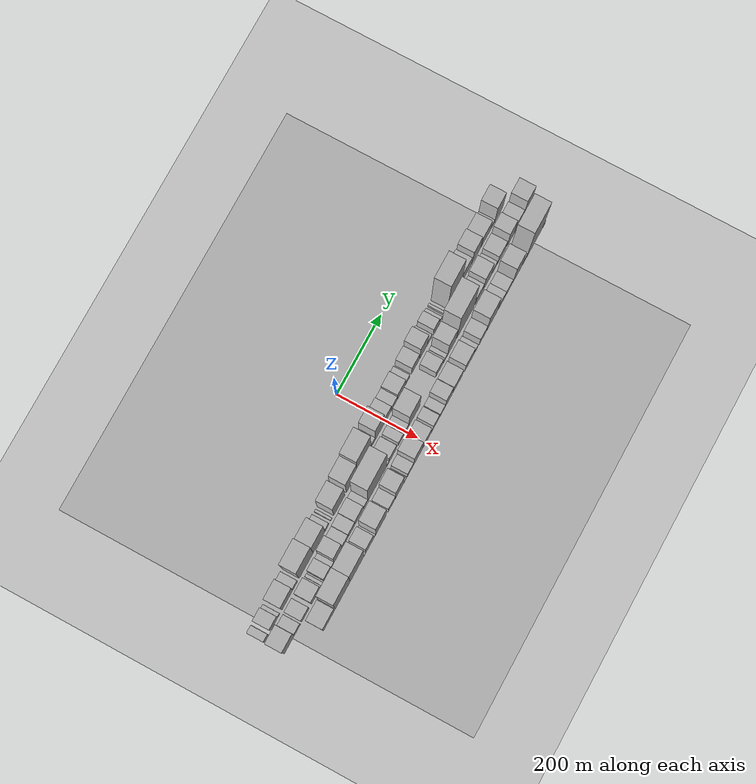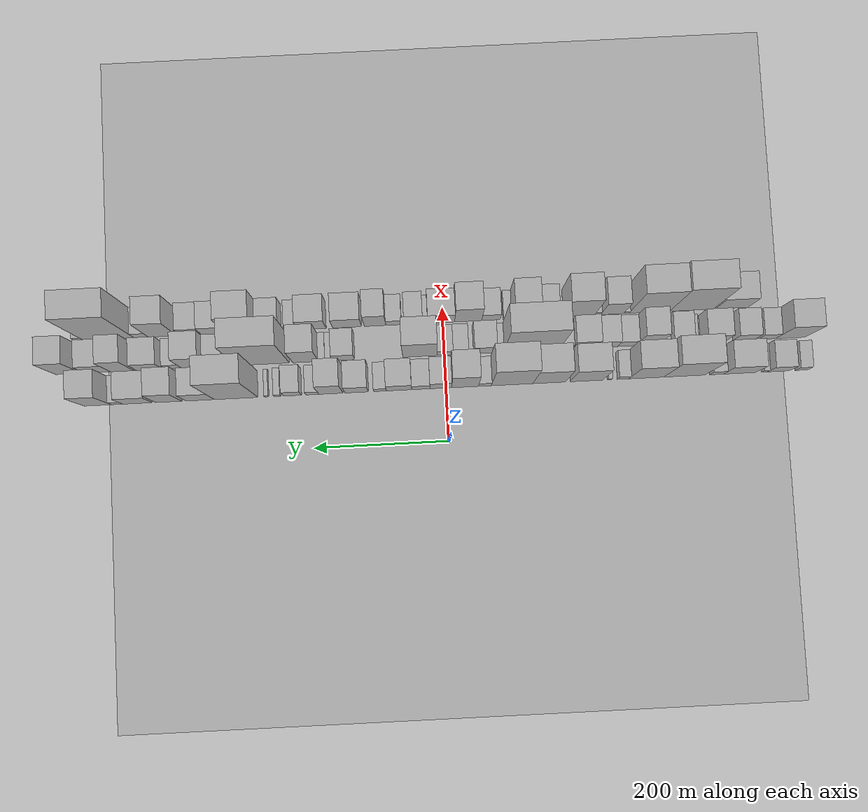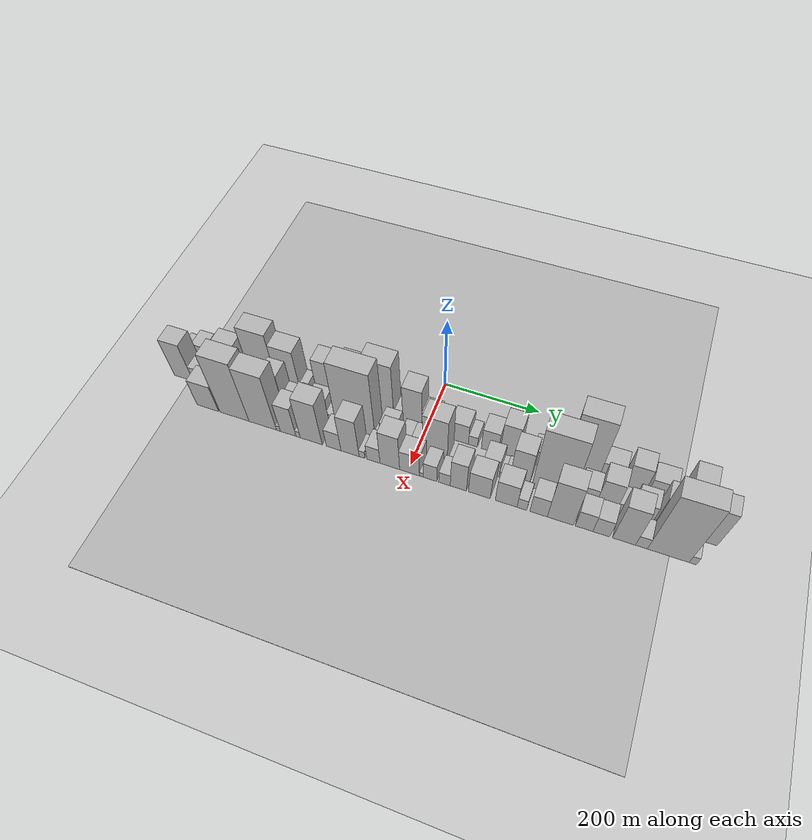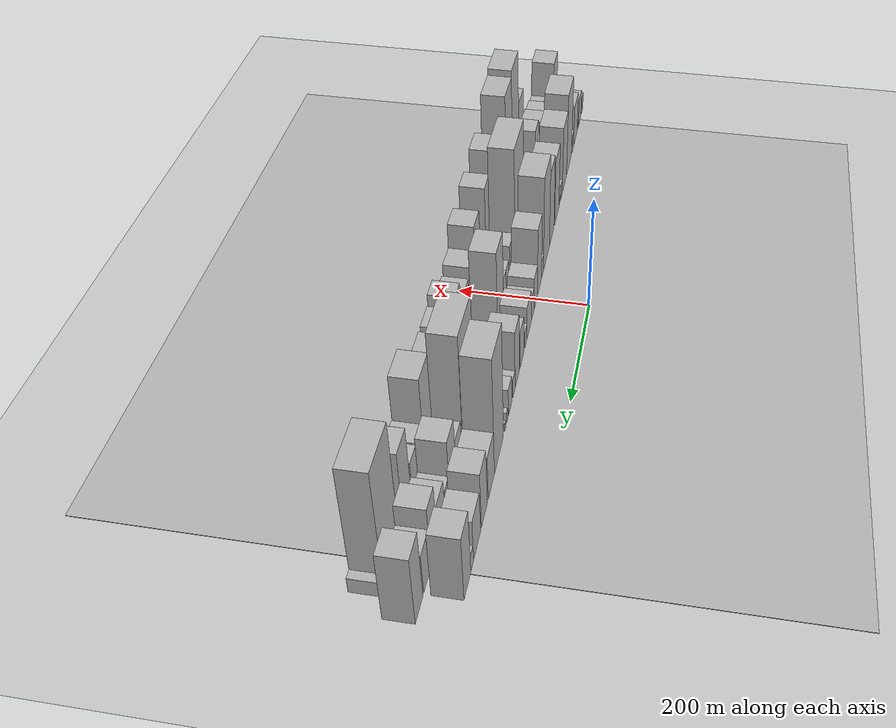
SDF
<?xml version="1.0" encoding="utf-8"?>

<sdf version="1.6">

   <world name="default">

      <gui fullscreen="0">

         <camera name="user_camera">

            <pose>-15 0 4.57585 0 0 0</pose>

            <view_controller>orbit</view_controller>

         </camera>

      </gui>

      <scene>

         <sky>

           <clouds>

             <speed>12</speed>

           </clouds>

         </sky>

         <ambient>0.4 0.4 0.4 1</ambient>

         <background>0.7 0.7 0.7 1</background>

         <shadows>1</shadows>

      </scene>

      <gravity>0 0 -9.8066</gravity>

      <magnetic_field>6e-06 2.3e-05 -4.2e-05</magnetic_field>

      <physics default="0" name="default_physics" type="ode">

         <ode>

            <solver>

               <type>quick</type>

               <iters>10</iters>

               <sor>1.0</sor>

               <use_dynamic_moi_rescaling>0</use_dynamic_moi_rescaling>

            </solver>

            <constraints>

               <cfm>0</cfm>

               <erp>0.2</erp>

               <contact_max_correcting_vel>100</contact_max_correcting_vel>

               <contact_surface_layer>0.001</contact_surface_layer>

            </constraints>

         </ode>

         <max_step_size>0.004</max_step_size>

         <real_time_factor>1</real_time_factor>

         <real_time_update_rate>250</real_time_update_rate>

      </physics>

      <light name="sun" type="directional">

         <cast_shadows>1</cast_shadows>

         <pose>0 0 10 0 0 0</pose>

         <diffuse>0.8 0.8 0.8 1</diffuse>

         <specular>0.2 0.2 0.2 1</specular>

         <attenuation>

            <range>1000</range>

            <constant>0.9</constant>

            <linear>0.01</linear>

            <quadratic>0.001</quadratic>

         </attenuation>

         <direction>-0.5 0.1 -0.9</direction>

      </light>

      <include>

         <name>ground_plane_1</name>

         <uri>model://HANNAS_ground_plane</uri>

         <pose>0 0 0  0 0 0</pose>

      </include>

      <include>

         <name>ground_plane_2</name>

         <uri>model://HANNAS_ground_plane</uri>

         <pose>100 0 0  0 0 0</pose>

      </include>

      <model name="building_1">

         <static>1</static>

         <pose frame="">100.0000 -526.7104 0 0.000000 0.000000 0.000000</pose>

         <link name="link">

            <pose frame="">0 0 18.00 0 0 0</pose>

            <collision name="collision">

               <geometry>

                  <box>

                     <size>40.0000 18.5791 36.0000</size>

                  </box>

               </geometry>

               <max_contacts>10</max_contacts>

               <surface>

                  <contact>

                     <ode/>

                  </contact>

                  <bounce/>

                  <friction>

                     <torsional>

                        <ode/>

                     </torsional>

                     <ode/>

                  </friction>

               </surface>

            </collision>

            <visual name="visual">

               <cast_shadows>0</cast_shadows>

               <geometry>

                  <box>

                     <size>40.0000 18.5791 36.0000</size>

                  </box>

               </geometry>

               <material>

                  <script>

                     <uri>model://HANNAS_wall/materials/scripts</uri>

                     <uri>model://HANNAS_wall/materials/textures</uri>

                     <name>vrc/HANNAS_wall</name>

                  </script>

               </material>

            </visual>

            <self_collide>0</self_collide>

            <enable_wind>0</enable_wind>

            <kinematic>0</kinematic>

         </link>

      </model>

      <model name="building_2">

         <static>1</static>

         <pose frame="">100.0000 -492.3587 0 0.000000 0.000000 0.000000</pose>

         <link name="link">

            <pose frame="">0 0 28.50 0 0 0</pose>

            <collision name="collision">

               <geometry>

                  <box>

                     <size>40.0000 32.1243 57.0000</size>

                  </box>

               </geometry>

               <max_contacts>10</max_contacts>

               <surface>

                  <contact>

                     <ode/>

                  </contact>

                  <bounce/>

                  <friction>

                     <torsional>

                        <ode/>

                     </torsional>

                     <ode/>

                  </friction>

               </surface>

            </collision>

            <visual name="visual">

               <cast_shadows>0</cast_shadows>

               <geometry>

                  <box>

                     <size>40.0000 32.1243 57.0000</size>

                  </box>

               </geometry>

               <material>

                  <script>

                     <uri>model://HANNAS_wall/materials/scripts</uri>

                     <uri>model://HANNAS_wall/materials/textures</uri>

                     <name>vrc/HANNAS_wall</name>

                  </script>

               </material>

            </visual>

            <self_collide>0</self_collide>

            <enable_wind>0</enable_wind>

            <kinematic>0</kinematic>

         </link>

      </model>

      <model name="building_3">

         <static>1</static>

         <pose frame="">100.0000 -471.9234 0 0.000000 0.000000 0.000000</pose>

         <link name="link">

            <pose frame="">0 0 10.50 0 0 0</pose>

            <collision name="collision">

               <geometry>

                  <box>

                     <size>40.0000 8.7463 21.0000</size>

                  </box>

               </geometry>

               <max_contacts>10</max_contacts>

               <surface>

                  <contact>

                     <ode/>

                  </contact>

                  <bounce/>

                  <friction>

                     <torsional>

                        <ode/>

                     </torsional>

                     <ode/>

                  </friction>

               </surface>

            </collision>

            <visual name="visual">

               <cast_shadows>0</cast_shadows>

               <geometry>

                  <box>

                     <size>40.0000 8.7463 21.0000</size>

                  </box>

               </geometry>

               <material>

                  <script>

                     <uri>model://HANNAS_wall/materials/scripts</uri>

                     <uri>model://HANNAS_wall/materials/textures</uri>

                     <name>vrc/HANNAS_wall</name>

                  </script>

               </material>

            </visual>

            <self_collide>0</self_collide>

            <enable_wind>0</enable_wind>

            <kinematic>0</kinematic>

         </link>

      </model>

      <model name="building_4">

         <static>1</static>

         <pose frame="">100.0000 -434.7010 0 0.000000 0.000000 0.000000</pose>

         <link name="link">

            <pose frame="">0 0 42.00 0 0 0</pose>

            <collision name="collision">

               <geometry>

                  <box>

                     <size>40.0000 47.6986 84.0000</size>

                  </box>

               </geometry>

               <max_contacts>10</max_contacts>

               <surface>

                  <contact>

                     <ode/>

                  </contact>

                  <bounce/>

                  <friction>

                     <torsional>

                        <ode/>

                     </torsional>

                     <ode/>

                  </friction>

               </surface>

            </collision>

            <visual name="visual">

               <cast_shadows>0</cast_shadows>

               <geometry>

                  <box>

                     <size>40.0000 47.6986 84.0000</size>

                  </box>

               </geometry>

               <material>

                  <script>

                     <uri>model://HANNAS_wall/materials/scripts</uri>

                     <uri>model://HANNAS_wall/materials/textures</uri>

                     <name>vrc/HANNAS_wall</name>

                  </script>

               </material>

            </visual>

            <self_collide>0</self_collide>

            <enable_wind>0</enable_wind>

            <kinematic>0</kinematic>

         </link>

      </model>

      <model name="building_5">

         <static>1</static>

         <pose frame="">100.0000 -400.5524 0 0.000000 0.000000 0.000000</pose>

         <link name="link">

            <pose frame="">0 0 18.00 0 0 0</pose>

            <collision name="collision">

               <geometry>

                  <box>

                     <size>40.0000 20.5985 36.0000</size>

                  </box>

               </geometry>

               <max_contacts>10</max_contacts>

               <surface>

                  <contact>

                     <ode/>

                  </contact>

                  <bounce/>

                  <friction>

                     <torsional>

                        <ode/>

                     </torsional>

                     <ode/>

                  </friction>

               </surface>

            </collision>

            <visual name="visual">

               <cast_shadows>0</cast_shadows>

               <geometry>

                  <box>

                     <size>40.0000 20.5985 36.0000</size>

                  </box>

               </geometry>

               <material>

                  <script>

                     <uri>model://HANNAS_wall/materials/scripts</uri>

                     <uri>model://HANNAS_wall/materials/textures</uri>

                     <name>vrc/HANNAS_wall</name>

                  </script>

               </material>

            </visual>

            <self_collide>0</self_collide>

            <enable_wind>0</enable_wind>

            <kinematic>0</kinematic>

         </link>

      </model>

      <model name="building_6">

         <static>1</static>

         <pose frame="">100.0000 -352.6470 0 0.000000 0.000000 0.000000</pose>

         <link name="link">

            <pose frame="">0 0 81.00 0 0 0</pose>

            <collision name="collision">

               <geometry>

                  <box>

                     <size>40.0000 61.2123 162.0000</size>

                  </box>

               </geometry>

               <max_contacts>10</max_contacts>

               <surface>

                  <contact>

                     <ode/>

                  </contact>

                  <bounce/>

                  <friction>

                     <torsional>

                        <ode/>

                     </torsional>

                     <ode/>

                  </friction>

               </surface>

            </collision>

            <visual name="visual">

               <cast_shadows>0</cast_shadows>

               <geometry>

                  <box>

                     <size>40.0000 61.2123 162.0000</size>

                  </box>

               </geometry>

               <material>

                  <script>

                     <uri>model://HANNAS_wall/materials/scripts</uri>

                     <uri>model://HANNAS_wall/materials/textures</uri>

                     <name>vrc/HANNAS_wall</name>

                  </script>

               </material>

            </visual>

            <self_collide>0</self_collide>

            <enable_wind>0</enable_wind>

            <kinematic>0</kinematic>

         </link>

      </model>

      <model name="building_7">

         <static>1</static>

         <pose frame="">100.0000 -296.2472 0 0.000000 0.000000 0.000000</pose>

         <link name="link">

            <pose frame="">0 0 66.00 0 0 0</pose>

            <collision name="collision">

               <geometry>

                  <box>

                     <size>40.0000 51.5875 132.0000</size>

                  </box>

               </geometry>

               <max_contacts>10</max_contacts>

               <surface>

                  <contact>

                     <ode/>

                  </contact>

                  <bounce/>

                  <friction>

                     <torsional>

                        <ode/>

                     </torsional>

                     <ode/>

                  </friction>

               </surface>

            </collision>

            <visual name="visual">

               <cast_shadows>0</cast_shadows>

               <geometry>

                  <box>

                     <size>40.0000 51.5875 132.0000</size>

                  </box>

               </geometry>

               <material>

                  <script>

                     <uri>model://HANNAS_wall/materials/scripts</uri>

                     <uri>model://HANNAS_wall/materials/textures</uri>

                     <name>vrc/HANNAS_wall</name>

                  </script>

               </material>

            </visual>

            <self_collide>0</self_collide>

            <enable_wind>0</enable_wind>

            <kinematic>0</kinematic>

         </link>

      </model>

      <model name="building_8">

         <static>1</static>

         <pose frame="">100.0000 -261.6943 0 0.000000 0.000000 0.000000</pose>

         <link name="link">

            <pose frame="">0 0 15.00 0 0 0</pose>

            <collision name="collision">

               <geometry>

                  <box>

                     <size>40.0000 17.5183 30.0000</size>

                  </box>

               </geometry>

               <max_contacts>10</max_contacts>

               <surface>

                  <contact>

                     <ode/>

                  </contact>

                  <bounce/>

                  <friction>

                     <torsional>

                        <ode/>

                     </torsional>

                     <ode/>

                  </friction>

               </surface>

            </collision>

            <visual name="visual">

               <cast_shadows>0</cast_shadows>

               <geometry>

                  <box>

                     <size>40.0000 17.5183 30.0000</size>

                  </box>

               </geometry>

               <material>

                  <script>

                     <uri>model://HANNAS_wall/materials/scripts</uri>

                     <uri>model://HANNAS_wall/materials/textures</uri>

                     <name>vrc/HANNAS_wall</name>

                  </script>

               </material>

            </visual>

            <self_collide>0</self_collide>

            <enable_wind>0</enable_wind>

            <kinematic>0</kinematic>

         </link>

      </model>

      <model name="building_9">

         <static>1</static>

         <pose frame="">100.0000 -241.7813 0 0.000000 0.000000 0.000000</pose>

         <link name="link">

            <pose frame="">0 0 7.50 0 0 0</pose>

            <collision name="collision">

               <geometry>

                  <box>

                     <size>40.0000 6.3077 15.0000</size>

                  </box>

               </geometry>

               <max_contacts>10</max_contacts>

               <surface>

                  <contact>

                     <ode/>

                  </contact>

                  <bounce/>

                  <friction>

                     <torsional>

                        <ode/>

                     </torsional>

                     <ode/>

                  </friction>

               </surface>

            </collision>

            <visual name="visual">

               <cast_shadows>0</cast_shadows>

               <geometry>

                  <box>

                     <size>40.0000 6.3077 15.0000</size>

                  </box>

               </geometry>

               <material>

                  <script>

                     <uri>model://HANNAS_wall/materials/scripts</uri>

                     <uri>model://HANNAS_wall/materials/textures</uri>

                     <name>vrc/HANNAS_wall</name>

                  </script>

               </material>

            </visual>

            <self_collide>0</self_collide>

            <enable_wind>0</enable_wind>

            <kinematic>0</kinematic>

         </link>

      </model>

      <model name="building_10">

         <static>1</static>

         <pose frame="">100.0000 -207.3583 0 0.000000 0.000000 0.000000</pose>

         <link name="link">

            <pose frame="">0 0 64.50 0 0 0</pose>

            <collision name="collision">

               <geometry>

                  <box>

                     <size>40.0000 48.5383 129.0000</size>

                  </box>

               </geometry>

               <max_contacts>10</max_contacts>

               <surface>

                  <contact>

                     <ode/>

                  </contact>

                  <bounce/>

                  <friction>

                     <torsional>

                        <ode/>

                     </torsional>

                     <ode/>

                  </friction>

               </surface>

            </collision>

            <visual name="visual">

               <cast_shadows>0</cast_shadows>

               <geometry>

                  <box>

                     <size>40.0000 48.5383 129.0000</size>

                  </box>

               </geometry>

               <material>

                  <script>

                     <uri>model://HANNAS_wall/materials/scripts</uri>

                     <uri>model://HANNAS_wall/materials/textures</uri>

                     <name>vrc/HANNAS_wall</name>

                  </script>

               </material>

            </visual>

            <self_collide>0</self_collide>

            <enable_wind>0</enable_wind>

            <kinematic>0</kinematic>

         </link>

      </model>

      <model name="building_11">

         <static>1</static>

         <pose frame="">100.0000 -151.8537 0 0.000000 0.000000 0.000000</pose>

         <link name="link">

            <pose frame="">0 0 72.00 0 0 0</pose>

            <collision name="collision">

               <geometry>

                  <box>

                     <size>40.0000 48.4710 144.0000</size>

                  </box>

               </geometry>

               <max_contacts>10</max_contacts>

               <surface>

                  <contact>

                     <ode/>

                  </contact>

                  <bounce/>

                  <friction>

                     <torsional>

                        <ode/>

                     </torsional>

                     <ode/>

                  </friction>

               </surface>

            </collision>

            <visual name="visual">

               <cast_shadows>0</cast_shadows>

               <geometry>

                  <box>

                     <size>40.0000 48.4710 144.0000</size>

                  </box>

               </geometry>

               <material>

                  <script>

                     <uri>model://HANNAS_wall/materials/scripts</uri>

                     <uri>model://HANNAS_wall/materials/textures</uri>

                     <name>vrc/HANNAS_wall</name>

                  </script>

               </material>

            </visual>

            <self_collide>0</self_collide>

            <enable_wind>0</enable_wind>

            <kinematic>0</kinematic>

         </link>

      </model>

      <model name="building_12">

         <static>1</static>

         <pose frame="">100.0000 -96.7841 0 0.000000 0.000000 0.000000</pose>

         <link name="link">

            <pose frame="">0 0 90.00 0 0 0</pose>

            <collision name="collision">

               <geometry>

                  <box>

                     <size>40.0000 61.6681 180.0000</size>

                  </box>

               </geometry>

               <max_contacts>10</max_contacts>

               <surface>

                  <contact>

                     <ode/>

                  </contact>

                  <bounce/>

                  <friction>

                     <torsional>

                        <ode/>

                     </torsional>

                     <ode/>

                  </friction>

               </surface>

            </collision>

            <visual name="visual">

               <cast_shadows>0</cast_shadows>

               <geometry>

                  <box>

                     <size>40.0000 61.6681 180.0000</size>

                  </box>

               </geometry>

               <material>

                  <script>

                     <uri>model://HANNAS_wall/materials/scripts</uri>

                     <uri>model://HANNAS_wall/materials/textures</uri>

                     <name>vrc/HANNAS_wall</name>

                  </script>

               </material>

            </visual>

            <self_collide>0</self_collide>

            <enable_wind>0</enable_wind>

            <kinematic>0</kinematic>

         </link>

      </model>

      <model name="building_13">

         <static>1</static>

         <pose frame="">100.0000 -56.4498 0 0.000000 0.000000 0.000000</pose>

         <link name="link">

            <pose frame="">0 0 18.00 0 0 0</pose>

            <collision name="collision">

               <geometry>

                  <box>

                     <size>40.0000 19.0006 36.0000</size>

                  </box>

               </geometry>

               <max_contacts>10</max_contacts>

               <surface>

                  <contact>

                     <ode/>

                  </contact>

                  <bounce/>

                  <friction>

                     <torsional>

                        <ode/>

                     </torsional>

                     <ode/>

                  </friction>

               </surface>

            </collision>

            <visual name="visual">

               <cast_shadows>0</cast_shadows>

               <geometry>

                  <box>

                     <size>40.0000 19.0006 36.0000</size>

                  </box>

               </geometry>

               <material>

                  <script>

                     <uri>model://HANNAS_wall/materials/scripts</uri>

                     <uri>model://HANNAS_wall/materials/textures</uri>

                     <name>vrc/HANNAS_wall</name>

                  </script>

               </material>

            </visual>

            <self_collide>0</self_collide>

            <enable_wind>0</enable_wind>

            <kinematic>0</kinematic>

         </link>

      </model>

      <model name="building_14">

         <static>1</static>

         <pose frame="">100.0000 -26.9856 0 0.000000 0.000000 0.000000</pose>

         <link name="link">

            <pose frame="">0 0 64.50 0 0 0</pose>

            <collision name="collision">

               <geometry>

                  <box>

                     <size>40.0000 39.9278 129.0000</size>

                  </box>

               </geometry>

               <max_contacts>10</max_contacts>

               <surface>

                  <contact>

                     <ode/>

                  </contact>

                  <bounce/>

                  <friction>

                     <torsional>

                        <ode/>

                     </torsional>

                     <ode/>

                  </friction>

               </surface>

            </collision>

            <visual name="visual">

               <cast_shadows>0</cast_shadows>

               <geometry>

                  <box>

                     <size>40.0000 39.9278 129.0000</size>

                  </box>

               </geometry>

               <material>

                  <script>

                     <uri>model://HANNAS_wall/materials/scripts</uri>

                     <uri>model://HANNAS_wall/materials/textures</uri>

                     <name>vrc/HANNAS_wall</name>

                  </script>

               </material>

            </visual>

            <self_collide>0</self_collide>

            <enable_wind>0</enable_wind>

            <kinematic>0</kinematic>

         </link>

      </model>

      <model name="building_15">

         <static>1</static>

         <pose frame="">100.0000 9.0524 0 0.000000 0.000000 0.000000</pose>

         <link name="link">

            <pose frame="">0 0 31.50 0 0 0</pose>

            <collision name="collision">

               <geometry>

                  <box>

                     <size>40.0000 32.1481 63.0000</size>

                  </box>

               </geometry>

               <max_contacts>10</max_contacts>

               <surface>

                  <contact>

                     <ode/>

                  </contact>

                  <bounce/>

                  <friction>

                     <torsional>

                        <ode/>

                     </torsional>

                     <ode/>

                  </friction>

               </surface>

            </collision>

            <visual name="visual">

               <cast_shadows>0</cast_shadows>

               <geometry>

                  <box>

                     <size>40.0000 32.1481 63.0000</size>

                  </box>

               </geometry>

               <material>

                  <script>

                     <uri>model://HANNAS_wall/materials/scripts</uri>

                     <uri>model://HANNAS_wall/materials/textures</uri>

                     <name>vrc/HANNAS_wall</name>

                  </script>

               </material>

            </visual>

            <self_collide>0</self_collide>

            <enable_wind>0</enable_wind>

            <kinematic>0</kinematic>

         </link>

      </model>

      <model name="building_16">

         <static>1</static>

         <pose frame="">100.0000 38.5215 0 0.000000 0.000000 0.000000</pose>

         <link name="link">

            <pose frame="">0 0 22.50 0 0 0</pose>

            <collision name="collision">

               <geometry>

                  <box>

                     <size>40.0000 26.7901 45.0000</size>

                  </box>

               </geometry>

               <max_contacts>10</max_contacts>

               <surface>

                  <contact>

                     <ode/>

                  </contact>

                  <bounce/>

                  <friction>

                     <torsional>

                        <ode/>

                     </torsional>

                     <ode/>

                  </friction>

               </surface>

            </collision>

            <visual name="visual">

               <cast_shadows>0</cast_shadows>

               <geometry>

                  <box>

                     <size>40.0000 26.7901 45.0000</size>

                  </box>

               </geometry>

               <material>

                  <script>

                     <uri>model://HANNAS_wall/materials/scripts</uri>

                     <uri>model://HANNAS_wall/materials/textures</uri>

                     <name>vrc/HANNAS_wall</name>

                  </script>

               </material>

            </visual>

            <self_collide>0</self_collide>

            <enable_wind>0</enable_wind>

            <kinematic>0</kinematic>

         </link>

      </model>

      <model name="building_17">

         <static>1</static>

         <pose frame="">100.0000 70.6206 0 0.000000 0.000000 0.000000</pose>

         <link name="link">

            <pose frame="">0 0 31.50 0 0 0</pose>

            <collision name="collision">

               <geometry>

                  <box>

                     <size>40.0000 37.4082 63.0000</size>

                  </box>

               </geometry>

               <max_contacts>10</max_contacts>

               <surface>

                  <contact>

                     <ode/>

                  </contact>

                  <bounce/>

                  <friction>

                     <torsional>

                        <ode/>

                     </torsional>

                     <ode/>

                  </friction>

               </surface>

            </collision>

            <visual name="visual">

               <cast_shadows>0</cast_shadows>

               <geometry>

                  <box>

                     <size>40.0000 37.4082 63.0000</size>

                  </box>

               </geometry>

               <material>

                  <script>

                     <uri>model://HANNAS_wall/materials/scripts</uri>

                     <uri>model://HANNAS_wall/materials/textures</uri>

                     <name>vrc/HANNAS_wall</name>

                  </script>

               </material>

            </visual>

            <self_collide>0</self_collide>

            <enable_wind>0</enable_wind>

            <kinematic>0</kinematic>

         </link>

      </model>

      <model name="building_18">

         <static>1</static>

         <pose frame="">100.0000 98.6573 0 0.000000 0.000000 0.000000</pose>

         <link name="link">

            <pose frame="">0 0 16.50 0 0 0</pose>

            <collision name="collision">

               <geometry>

                  <box>

                     <size>40.0000 18.6651 33.0000</size>

                  </box>

               </geometry>

               <max_contacts>10</max_contacts>

               <surface>

                  <contact>

                     <ode/>

                  </contact>

                  <bounce/>

                  <friction>

                     <torsional>

                        <ode/>

                     </torsional>

                     <ode/>

                  </friction>

               </surface>

            </collision>

            <visual name="visual">

               <cast_shadows>0</cast_shadows>

               <geometry>

                  <box>

                     <size>40.0000 18.6651 33.0000</size>

                  </box>

               </geometry>

               <material>

                  <script>

                     <uri>model://HANNAS_wall/materials/scripts</uri>

                     <uri>model://HANNAS_wall/materials/textures</uri>

                     <name>vrc/HANNAS_wall</name>

                  </script>

               </material>

            </visual>

            <self_collide>0</self_collide>

            <enable_wind>0</enable_wind>

            <kinematic>0</kinematic>

         </link>

      </model>

      <model name="building_19">

         <static>1</static>

         <pose frame="">100.0000 133.3318 0 0.000000 0.000000 0.000000</pose>

         <link name="link">

            <pose frame="">0 0 34.50 0 0 0</pose>

            <collision name="collision">

               <geometry>

                  <box>

                     <size>40.0000 34.6839 69.0000</size>

                  </box>

               </geometry>

               <max_contacts>10</max_contacts>

               <surface>

                  <contact>

                     <ode/>

                  </contact>

                  <bounce/>

                  <friction>

                     <torsional>

                        <ode/>

                     </torsional>

                     <ode/>

                  </friction>

               </surface>

            </collision>

            <visual name="visual">

               <cast_shadows>0</cast_shadows>

               <geometry>

                  <box>

                     <size>40.0000 34.6839 69.0000</size>

                  </box>

               </geometry>

               <material>

                  <script>

                     <uri>model://HANNAS_wall/materials/scripts</uri>

                     <uri>model://HANNAS_wall/materials/textures</uri>

                     <name>vrc/HANNAS_wall</name>

                  </script>

               </material>

            </visual>

            <self_collide>0</self_collide>

            <enable_wind>0</enable_wind>

            <kinematic>0</kinematic>

         </link>

      </model>

      <model name="building_20">

         <static>1</static>

         <pose frame="">100.0000 171.4548 0 0.000000 0.000000 0.000000</pose>

         <link name="link">

            <pose frame="">0 0 54.00 0 0 0</pose>

            <collision name="collision">

               <geometry>

                  <box>

                     <size>40.0000 35.5620 108.0000</size>

                  </box>

               </geometry>

               <max_contacts>10</max_contacts>

               <surface>

                  <contact>

                     <ode/>

                  </contact>

                  <bounce/>

                  <friction>

                     <torsional>

                        <ode/>

                     </torsional>

                     <ode/>

                  </friction>

               </surface>

            </collision>

            <visual name="visual">

               <cast_shadows>0</cast_shadows>

               <geometry>

                  <box>

                     <size>40.0000 35.5620 108.0000</size>

                  </box>

               </geometry>

               <material>

                  <script>

                     <uri>model://HANNAS_wall/materials/scripts</uri>

                     <uri>model://HANNAS_wall/materials/textures</uri>

                     <name>vrc/HANNAS_wall</name>

                  </script>

               </material>

            </visual>

            <self_collide>0</self_collide>

            <enable_wind>0</enable_wind>

            <kinematic>0</kinematic>

         </link>

      </model>

      <model name="building_21">

         <static>1</static>

         <pose frame="">100.0000 198.6346 0 0.000000 0.000000 0.000000</pose>

         <link name="link">

            <pose frame="">0 0 18.00 0 0 0</pose>

            <collision name="collision">

               <geometry>

                  <box>

                     <size>40.0000 18.7976 36.0000</size>

                  </box>

               </geometry>

               <max_contacts>10</max_contacts>

               <surface>

                  <contact>

                     <ode/>

                  </contact>

                  <bounce/>

                  <friction>

                     <torsional>

                        <ode/>

                     </torsional>

                     <ode/>

                  </friction>

               </surface>

            </collision>

            <visual name="visual">

               <cast_shadows>0</cast_shadows>

               <geometry>

                  <box>

                     <size>40.0000 18.7976 36.0000</size>

                  </box>

               </geometry>

               <material>

                  <script>

                     <uri>model://HANNAS_wall/materials/scripts</uri>

                     <uri>model://HANNAS_wall/materials/textures</uri>

                     <name>vrc/HANNAS_wall</name>

                  </script>

               </material>

            </visual>

            <self_collide>0</self_collide>

            <enable_wind>0</enable_wind>

            <kinematic>0</kinematic>

         </link>

      </model>

      <model name="building_22">

         <static>1</static>

         <pose frame="">100.0000 228.3697 0 0.000000 0.000000 0.000000</pose>

         <link name="link">

            <pose frame="">0 0 25.50 0 0 0</pose>

            <collision name="collision">

               <geometry>

                  <box>

                     <size>40.0000 26.6725 51.0000</size>

                  </box>

               </geometry>

               <max_contacts>10</max_contacts>

               <surface>

                  <contact>

                     <ode/>

                  </contact>

                  <bounce/>

                  <friction>

                     <torsional>

                        <ode/>

                     </torsional>

                     <ode/>

                  </friction>

               </surface>

            </collision>

            <visual name="visual">

               <cast_shadows>0</cast_shadows>

               <geometry>

                  <box>

                     <size>40.0000 26.6725 51.0000</size>

                  </box>

               </geometry>

               <material>

                  <script>

                     <uri>model://HANNAS_wall/materials/scripts</uri>

                     <uri>model://HANNAS_wall/materials/textures</uri>

                     <name>vrc/HANNAS_wall</name>

                  </script>

               </material>

            </visual>

            <self_collide>0</self_collide>

            <enable_wind>0</enable_wind>

            <kinematic>0</kinematic>

         </link>

      </model>

      <model name="building_23">

         <static>1</static>

         <pose frame="">100.0000 250.6202 0 0.000000 0.000000 0.000000</pose>

         <link name="link">

            <pose frame="">0 0 10.50 0 0 0</pose>

            <collision name="collision">

               <geometry>

                  <box>

                     <size>40.0000 9.8286 21.0000</size>

                  </box>

               </geometry>

               <max_contacts>10</max_contacts>

               <surface>

                  <contact>

                     <ode/>

                  </contact>

                  <bounce/>

                  <friction>

                     <torsional>

                        <ode/>

                     </torsional>

                     <ode/>

                  </friction>

               </surface>

            </collision>

            <visual name="visual">

               <cast_shadows>0</cast_shadows>

               <geometry>

                  <box>

                     <size>40.0000 9.8286 21.0000</size>

                  </box>

               </geometry>

               <material>

                  <script>

                     <uri>model://HANNAS_wall/materials/scripts</uri>

                     <uri>model://HANNAS_wall/materials/textures</uri>

                     <name>vrc/HANNAS_wall</name>

                  </script>

               </material>

            </visual>

            <self_collide>0</self_collide>

            <enable_wind>0</enable_wind>

            <kinematic>0</kinematic>

         </link>

      </model>

      <model name="building_24">

         <static>1</static>

         <pose frame="">100.0000 266.6115 0 0.000000 0.000000 0.000000</pose>

         <link name="link">

            <pose frame="">0 0 7.50 0 0 0</pose>

            <collision name="collision">

               <geometry>

                  <box>

                     <size>40.0000 6.1540 15.0000</size>

                  </box>

               </geometry>

               <max_contacts>10</max_contacts>

               <surface>

                  <contact>

                     <ode/>

                  </contact>

                  <bounce/>

                  <friction>

                     <torsional>

                        <ode/>

                     </torsional>

                     <ode/>

                  </friction>

               </surface>

            </collision>

            <visual name="visual">

               <cast_shadows>0</cast_shadows>

               <geometry>

                  <box>

                     <size>40.0000 6.1540 15.0000</size>

                  </box>

               </geometry>

               <material>

                  <script>

                     <uri>model://HANNAS_wall/materials/scripts</uri>

                     <uri>model://HANNAS_wall/materials/textures</uri>

                     <name>vrc/HANNAS_wall</name>

                  </script>

               </material>

            </visual>

            <self_collide>0</self_collide>

            <enable_wind>0</enable_wind>

            <kinematic>0</kinematic>

         </link>

      </model>

      <model name="building_25">

         <static>1</static>

         <pose frame="">100.0000 312.0021 0 0.000000 0.000000 0.000000</pose>

         <link name="link">

            <pose frame="">0 0 105.00 0 0 0</pose>

            <collision name="collision">

               <geometry>

                  <box>

                     <size>40.0000 64.6272 210.0000</size>

                  </box>

               </geometry>

               <max_contacts>10</max_contacts>

               <surface>

                  <contact>

                     <ode/>

                  </contact>

                  <bounce/>

                  <friction>

                     <torsional>

                        <ode/>

                     </torsional>

                     <ode/>

                  </friction>

               </surface>

            </collision>

            <visual name="visual">

               <cast_shadows>0</cast_shadows>

               <geometry>

                  <box>

                     <size>40.0000 64.6272 210.0000</size>

                  </box>

               </geometry>

               <material>

                  <script>

                     <uri>model://HANNAS_wall/materials/scripts</uri>

                     <uri>model://HANNAS_wall/materials/textures</uri>

                     <name>vrc/HANNAS_wall</name>

                  </script>

               </material>

            </visual>

            <self_collide>0</self_collide>

            <enable_wind>0</enable_wind>

            <kinematic>0</kinematic>

         </link>

      </model>

      <model name="building_26">

         <static>1</static>

         <pose frame="">100.0000 365.3880 0 0.000000 0.000000 0.000000</pose>

         <link name="link">

            <pose frame="">0 0 40.50 0 0 0</pose>

            <collision name="collision">

               <geometry>

                  <box>

                     <size>40.0000 42.1446 81.0000</size>

                  </box>

               </geometry>

               <max_contacts>10</max_contacts>

               <surface>

                  <contact>

                     <ode/>

                  </contact>

                  <bounce/>

                  <friction>

                     <torsional>

                        <ode/>

                     </torsional>

                     <ode/>

                  </friction>

               </surface>

            </collision>

            <visual name="visual">

               <cast_shadows>0</cast_shadows>

               <geometry>

                  <box>

                     <size>40.0000 42.1446 81.0000</size>

                  </box>

               </geometry>

               <material>

                  <script>

                     <uri>model://HANNAS_wall/materials/scripts</uri>

                     <uri>model://HANNAS_wall/materials/textures</uri>

                     <name>vrc/HANNAS_wall</name>

                  </script>

               </material>

            </visual>

            <self_collide>0</self_collide>

            <enable_wind>0</enable_wind>

            <kinematic>0</kinematic>

         </link>

      </model>

      <model name="building_27">

         <static>1</static>

         <pose frame="">100.0000 411.8133 0 0.000000 0.000000 0.000000</pose>

         <link name="link">

            <pose frame="">0 0 51.00 0 0 0</pose>

            <collision name="collision">

               <geometry>

                  <box>

                     <size>40.0000 38.7061 102.0000</size>

                  </box>

               </geometry>

               <max_contacts>10</max_contacts>

               <surface>

                  <contact>

                     <ode/>

                  </contact>

                  <bounce/>

                  <friction>

                     <torsional>

                        <ode/>

                     </torsional>

                     <ode/>

                  </friction>

               </surface>

            </collision>

            <visual name="visual">

               <cast_shadows>0</cast_shadows>

               <geometry>

                  <box>

                     <size>40.0000 38.7061 102.0000</size>

                  </box>

               </geometry>

               <material>

                  <script>

                     <uri>model://HANNAS_wall/materials/scripts</uri>

                     <uri>model://HANNAS_wall/materials/textures</uri>

                     <name>vrc/HANNAS_wall</name>

                  </script>

               </material>

            </visual>

            <self_collide>0</self_collide>

            <enable_wind>0</enable_wind>

            <kinematic>0</kinematic>

         </link>

      </model>

      <model name="building_28">

         <static>1</static>

         <pose frame="">100.0000 458.0838 0 0.000000 0.000000 0.000000</pose>

         <link name="link">

            <pose frame="">0 0 37.50 0 0 0</pose>

            <collision name="collision">

               <geometry>

                  <box>

                     <size>40.0000 43.8348 75.0000</size>

                  </box>

               </geometry>

               <max_contacts>10</max_contacts>

               <surface>

                  <contact>

                     <ode/>

                  </contact>

                  <bounce/>

                  <friction>

                     <torsional>

                        <ode/>

                     </torsional>

                     <ode/>

                  </friction>

               </surface>

            </collision>

            <visual name="visual">

               <cast_shadows>0</cast_shadows>

               <geometry>

                  <box>

                     <size>40.0000 43.8348 75.0000</size>

                  </box>

               </geometry>

               <material>

                  <script>

                     <uri>model://HANNAS_wall/materials/scripts</uri>

                     <uri>model://HANNAS_wall/materials/textures</uri>

                     <name>vrc/HANNAS_wall</name>

                  </script>

               </material>

            </visual>

            <self_collide>0</self_collide>

            <enable_wind>0</enable_wind>

            <kinematic>0</kinematic>

         </link>

      </model>

      <model name="building_29">

         <static>1</static>

         <pose frame="">100.0000 488.4881 0 0.000000 0.000000 0.000000</pose>

         <link name="link">

            <pose frame="">0 0 15.00 0 0 0</pose>

            <collision name="collision">

               <geometry>

                  <box>

                     <size>40.0000 16.9738 30.0000</size>

                  </box>

               </geometry>

               <max_contacts>10</max_contacts>

               <surface>

                  <contact>

                     <ode/>

                  </contact>

                  <bounce/>

                  <friction>

                     <torsional>

                        <ode/>

                     </torsional>

                     <ode/>

                  </friction>

               </surface>

            </collision>

            <visual name="visual">

               <cast_shadows>0</cast_shadows>

               <geometry>

                  <box>

                     <size>40.0000 16.9738 30.0000</size>

                  </box>

               </geometry>

               <material>

                  <script>

                     <uri>model://HANNAS_wall/materials/scripts</uri>

                     <uri>model://HANNAS_wall/materials/textures</uri>

                     <name>vrc/HANNAS_wall</name>

                  </script>

               </material>

            </visual>

            <self_collide>0</self_collide>

            <enable_wind>0</enable_wind>

            <kinematic>0</kinematic>

         </link>

      </model>

      <model name="building_30">

         <static>1</static>

         <pose frame="">100.0000 516.9456 0 0.000000 0.000000 0.000000</pose>

         <link name="link">

            <pose frame="">0 0 58.50 0 0 0</pose>

            <collision name="collision">

               <geometry>

                  <box>

                     <size>40.0000 39.9413 117.0000</size>

                  </box>

               </geometry>

               <max_contacts>10</max_contacts>

               <surface>

                  <contact>

                     <ode/>

                  </contact>

                  <bounce/>

                  <friction>

                     <torsional>

                        <ode/>

                     </torsional>

                     <ode/>

                  </friction>

               </surface>

            </collision>

            <visual name="visual">

               <cast_shadows>0</cast_shadows>

               <geometry>

                  <box>

                     <size>40.0000 39.9413 117.0000</size>

                  </box>

               </geometry>

               <material>

                  <script>

                     <uri>model://HANNAS_wall/materials/scripts</uri>

                     <uri>model://HANNAS_wall/materials/textures</uri>

                     <name>vrc/HANNAS_wall</name>

                  </script>

               </material>

            </visual>

            <self_collide>0</self_collide>

            <enable_wind>0</enable_wind>

            <kinematic>0</kinematic>

         </link>

      </model>

      <model name="building_31">

         <static>1</static>

         <pose frame="">149.0000 -513.9039 0 0.000000 0.000000 0.000000</pose>

         <link name="link">

            <pose frame="">0 0 58.50 0 0 0</pose>

            <collision name="collision">

               <geometry>

                  <box>

                     <size>40.0000 44.1923 117.0000</size>

                  </box>

               </geometry>

               <max_contacts>10</max_contacts>

               <surface>

                  <contact>

                     <ode/>

                  </contact>

                  <bounce/>

                  <friction>

                     <torsional>

                        <ode/>

                     </torsional>

                     <ode/>

                  </friction>

               </surface>

            </collision>

            <visual name="visual">

               <cast_shadows>0</cast_shadows>

               <geometry>

                  <box>

                     <size>40.0000 44.1923 117.0000</size>

                  </box>

               </geometry>

               <material>

                  <script>

                     <uri>model://HANNAS_wall/materials/scripts</uri>

                     <uri>model://HANNAS_wall/materials/textures</uri>

                     <name>vrc/HANNAS_wall</name>

                  </script>

               </material>

            </visual>

            <self_collide>0</self_collide>

            <enable_wind>0</enable_wind>

            <kinematic>0</kinematic>

         </link>

      </model>

      <model name="building_32">

         <static>1</static>

         <pose frame="">149.0000 -478.8391 0 0.000000 0.000000 0.000000</pose>

         <link name="link">

            <pose frame="">0 0 24.00 0 0 0</pose>

            <collision name="collision">

               <geometry>

                  <box>

                     <size>40.0000 25.9372 48.0000</size>

                  </box>

               </geometry>

               <max_contacts>10</max_contacts>

               <surface>

                  <contact>

                     <ode/>

                  </contact>

                  <bounce/>

                  <friction>

                     <torsional>

                        <ode/>

                     </torsional>

                     <ode/>

                  </friction>

               </surface>

            </collision>

            <visual name="visual">

               <cast_shadows>0</cast_shadows>

               <geometry>

                  <box>

                     <size>40.0000 25.9372 48.0000</size>

                  </box>

               </geometry>

               <material>

                  <script>

                     <uri>model://HANNAS_wall/materials/scripts</uri>

                     <uri>model://HANNAS_wall/materials/textures</uri>

                     <name>vrc/HANNAS_wall</name>

                  </script>

               </material>

            </visual>

            <self_collide>0</self_collide>

            <enable_wind>0</enable_wind>

            <kinematic>0</kinematic>

         </link>

      </model>

      <model name="building_33">

         <static>1</static>

         <pose frame="">149.0000 -444.4173 0 0.000000 0.000000 0.000000</pose>

         <link name="link">

            <pose frame="">0 0 28.50 0 0 0</pose>

            <collision name="collision">

               <geometry>

                  <box>

                     <size>40.0000 32.9065 57.0000</size>

                  </box>

               </geometry>

               <max_contacts>10</max_contacts>

               <surface>

                  <contact>

                     <ode/>

                  </contact>

                  <bounce/>

                  <friction>

                     <torsional>

                        <ode/>

                     </torsional>

                     <ode/>

                  </friction>

               </surface>

            </collision>

            <visual name="visual">

               <cast_shadows>0</cast_shadows>

               <geometry>

                  <box>

                     <size>40.0000 32.9065 57.0000</size>

                  </box>

               </geometry>

               <material>

                  <script>

                     <uri>model://HANNAS_wall/materials/scripts</uri>

                     <uri>model://HANNAS_wall/materials/textures</uri>

                     <name>vrc/HANNAS_wall</name>

                  </script>

               </material>

            </visual>

            <self_collide>0</self_collide>

            <enable_wind>0</enable_wind>

            <kinematic>0</kinematic>

         </link>

      </model>

      <model name="building_34">

         <static>1</static>

         <pose frame="">149.0000 -398.9525 0 0.000000 0.000000 0.000000</pose>

         <link name="link">

            <pose frame="">0 0 33.00 0 0 0</pose>

            <collision name="collision">

               <geometry>

                  <box>

                     <size>40.0000 38.0232 66.0000</size>

                  </box>

               </geometry>

               <max_contacts>10</max_contacts>

               <surface>

                  <contact>

                     <ode/>

                  </contact>

                  <bounce/>

                  <friction>

                     <torsional>

                        <ode/>

                     </torsional>

                     <ode/>

                  </friction>

               </surface>

            </collision>

            <visual name="visual">

               <cast_shadows>0</cast_shadows>

               <geometry>

                  <box>

                     <size>40.0000 38.0232 66.0000</size>

                  </box>

               </geometry>

               <material>

                  <script>

                     <uri>model://HANNAS_wall/materials/scripts</uri>

                     <uri>model://HANNAS_wall/materials/textures</uri>

                     <name>vrc/HANNAS_wall</name>

                  </script>

               </material>

            </visual>

            <self_collide>0</self_collide>

            <enable_wind>0</enable_wind>

            <kinematic>0</kinematic>

         </link>

      </model>

      <model name="building_35">

         <static>1</static>

         <pose frame="">149.0000 -371.0271 0 0.000000 0.000000 0.000000</pose>

         <link name="link">

            <pose frame="">0 0 9.00 0 0 0</pose>

            <collision name="collision">

               <geometry>

                  <box>

                     <size>40.0000 7.8276 18.0000</size>

                  </box>

               </geometry>

               <max_contacts>10</max_contacts>

               <surface>

                  <contact>

                     <ode/>

                  </contact>

                  <bounce/>

                  <friction>

                     <torsional>

                        <ode/>

                     </torsional>

                     <ode/>

                  </friction>

               </surface>

            </collision>

            <visual name="visual">

               <cast_shadows>0</cast_shadows>

               <geometry>

                  <box>

                     <size>40.0000 7.8276 18.0000</size>

                  </box>

               </geometry>

               <material>

                  <script>

                     <uri>model://HANNAS_wall/materials/scripts</uri>

                     <uri>model://HANNAS_wall/materials/textures</uri>

                     <name>vrc/HANNAS_wall</name>

                  </script>

               </material>

            </visual>

            <self_collide>0</self_collide>

            <enable_wind>0</enable_wind>

            <kinematic>0</kinematic>

         </link>

      </model>

      <model name="building_36">

         <static>1</static>

         <pose frame="">149.0000 -347.7854 0 0.000000 0.000000 0.000000</pose>

         <link name="link">

            <pose frame="">0 0 28.50 0 0 0</pose>

            <collision name="collision">

               <geometry>

                  <box>

                     <size>40.0000 30.6557 57.0000</size>

                  </box>

               </geometry>

               <max_contacts>10</max_contacts>

               <surface>

                  <contact>

                     <ode/>

                  </contact>

                  <bounce/>

                  <friction>

                     <torsional>

                        <ode/>

                     </torsional>

                     <ode/>

                  </friction>

               </surface>

            </collision>

            <visual name="visual">

               <cast_shadows>0</cast_shadows>

               <geometry>

                  <box>

                     <size>40.0000 30.6557 57.0000</size>

                  </box>

               </geometry>

               <material>

                  <script>

                     <uri>model://HANNAS_wall/materials/scripts</uri>

                     <uri>model://HANNAS_wall/materials/textures</uri>

                     <name>vrc/HANNAS_wall</name>

                  </script>

               </material>

            </visual>

            <self_collide>0</self_collide>

            <enable_wind>0</enable_wind>

            <kinematic>0</kinematic>

         </link>

      </model>

      <model name="building_37">

         <static>1</static>

         <pose frame="">149.0000 -325.7199 0 0.000000 0.000000 0.000000</pose>

         <link name="link">

            <pose frame="">0 0 13.50 0 0 0</pose>

            <collision name="collision">

               <geometry>

                  <box>

                     <size>40.0000 13.4754 27.0000</size>

                  </box>

               </geometry>

               <max_contacts>10</max_contacts>

               <surface>

                  <contact>

                     <ode/>

                  </contact>

                  <bounce/>

                  <friction>

                     <torsional>

                        <ode/>

                     </torsional>

                     <ode/>

                  </friction>

               </surface>

            </collision>

            <visual name="visual">

               <cast_shadows>0</cast_shadows>

               <geometry>

                  <box>

                     <size>40.0000 13.4754 27.0000</size>

                  </box>

               </geometry>

               <material>

                  <script>

                     <uri>model://HANNAS_wall/materials/scripts</uri>

                     <uri>model://HANNAS_wall/materials/textures</uri>

                     <name>vrc/HANNAS_wall</name>

                  </script>

               </material>

            </visual>

            <self_collide>0</self_collide>

            <enable_wind>0</enable_wind>

            <kinematic>0</kinematic>

         </link>

      </model>

      <model name="building_38">

         <static>1</static>

         <pose frame="">149.0000 -301.5186 0 0.000000 0.000000 0.000000</pose>

         <link name="link">

            <pose frame="">0 0 55.50 0 0 0</pose>

            <collision name="collision">

               <geometry>

                  <box>

                     <size>40.0000 34.9273 111.0000</size>

                  </box>

               </geometry>

               <max_contacts>10</max_contacts>

               <surface>

                  <contact>

                     <ode/>

                  </contact>

                  <bounce/>

                  <friction>

                     <torsional>

                        <ode/>

                     </torsional>

                     <ode/>

                  </friction>

               </surface>

            </collision>

            <visual name="visual">

               <cast_shadows>0</cast_shadows>

               <geometry>

                  <box>

                     <size>40.0000 34.9273 111.0000</size>

                  </box>

               </geometry>

               <material>

                  <script>

                     <uri>model://HANNAS_wall/materials/scripts</uri>

                     <uri>model://HANNAS_wall/materials/textures</uri>

                     <name>vrc/HANNAS_wall</name>

                  </script>

               </material>

            </visual>

            <self_collide>0</self_collide>

            <enable_wind>0</enable_wind>

            <kinematic>0</kinematic>

         </link>

      </model>

      <model name="building_39">

         <static>1</static>

         <pose frame="">149.0000 -270.4646 0 0.000000 0.000000 0.000000</pose>

         <link name="link">

            <pose frame="">0 0 24.00 0 0 0</pose>

            <collision name="collision">

               <geometry>

                  <box>

                     <size>40.0000 27.1806 48.0000</size>

                  </box>

               </geometry>

               <max_contacts>10</max_contacts>

               <surface>

                  <contact>

                     <ode/>

                  </contact>

                  <bounce/>

                  <friction>

                     <torsional>

                        <ode/>

                     </torsional>

                     <ode/>

                  </friction>

               </surface>

            </collision>

            <visual name="visual">

               <cast_shadows>0</cast_shadows>

               <geometry>

                  <box>

                     <size>40.0000 27.1806 48.0000</size>

                  </box>

               </geometry>

               <material>

                  <script>

                     <uri>model://HANNAS_wall/materials/scripts</uri>

                     <uri>model://HANNAS_wall/materials/textures</uri>

                     <name>vrc/HANNAS_wall</name>

                  </script>

               </material>

            </visual>

            <self_collide>0</self_collide>

            <enable_wind>0</enable_wind>

            <kinematic>0</kinematic>

         </link>

      </model>

      <model name="building_40">

         <static>1</static>

         <pose frame="">149.0000 -241.8862 0 0.000000 0.000000 0.000000</pose>

         <link name="link">

            <pose frame="">0 0 28.50 0 0 0</pose>

            <collision name="collision">

               <geometry>

                  <box>

                     <size>40.0000 29.9763 57.0000</size>

                  </box>

               </geometry>

               <max_contacts>10</max_contacts>

               <surface>

                  <contact>

                     <ode/>

                  </contact>

                  <bounce/>

                  <friction>

                     <torsional>

                        <ode/>

                     </torsional>

                     <ode/>

                  </friction>

               </surface>

            </collision>

            <visual name="visual">

               <cast_shadows>0</cast_shadows>

               <geometry>

                  <box>

                     <size>40.0000 29.9763 57.0000</size>

                  </box>

               </geometry>

               <material>

                  <script>

                     <uri>model://HANNAS_wall/materials/scripts</uri>

                     <uri>model://HANNAS_wall/materials/textures</uri>

                     <name>vrc/HANNAS_wall</name>

                  </script>

               </material>

            </visual>

            <self_collide>0</self_collide>

            <enable_wind>0</enable_wind>

            <kinematic>0</kinematic>

         </link>

      </model>

      <model name="building_41">

         <static>1</static>

         <pose frame="">149.0000 -208.3323 0 0.000000 0.000000 0.000000</pose>

         <link name="link">

            <pose frame="">0 0 34.50 0 0 0</pose>

            <collision name="collision">

               <geometry>

                  <box>

                     <size>40.0000 37.1314 69.0000</size>

                  </box>

               </geometry>

               <max_contacts>10</max_contacts>

               <surface>

                  <contact>

                     <ode/>

                  </contact>

                  <bounce/>

                  <friction>

                     <torsional>

                        <ode/>

                     </torsional>

                     <ode/>

                  </friction>

               </surface>

            </collision>

            <visual name="visual">

               <cast_shadows>0</cast_shadows>

               <geometry>

                  <box>

                     <size>40.0000 37.1314 69.0000</size>

                  </box>

               </geometry>

               <material>

                  <script>

                     <uri>model://HANNAS_wall/materials/scripts</uri>

                     <uri>model://HANNAS_wall/materials/textures</uri>

                     <name>vrc/HANNAS_wall</name>

                  </script>

               </material>

            </visual>

            <self_collide>0</self_collide>

            <enable_wind>0</enable_wind>

            <kinematic>0</kinematic>

         </link>

      </model>

      <model name="building_42">

         <static>1</static>

         <pose frame="">149.0000 -179.9812 0 0.000000 0.000000 0.000000</pose>

         <link name="link">

            <pose frame="">0 0 18.00 0 0 0</pose>

            <collision name="collision">

               <geometry>

                  <box>

                     <size>40.0000 19.5709 36.0000</size>

                  </box>

               </geometry>

               <max_contacts>10</max_contacts>

               <surface>

                  <contact>

                     <ode/>

                  </contact>

                  <bounce/>

                  <friction>

                     <torsional>

                        <ode/>

                     </torsional>

                     <ode/>

                  </friction>

               </surface>

            </collision>

            <visual name="visual">

               <cast_shadows>0</cast_shadows>

               <geometry>

                  <box>

                     <size>40.0000 19.5709 36.0000</size>

                  </box>

               </geometry>

               <material>

                  <script>

                     <uri>model://HANNAS_wall/materials/scripts</uri>

                     <uri>model://HANNAS_wall/materials/textures</uri>

                     <name>vrc/HANNAS_wall</name>

                  </script>

               </material>

            </visual>

            <self_collide>0</self_collide>

            <enable_wind>0</enable_wind>

            <kinematic>0</kinematic>

         </link>

      </model>

      <model name="building_43">

         <static>1</static>

         <pose frame="">149.0000 -128.4672 0 0.000000 0.000000 0.000000</pose>

         <link name="link">

            <pose frame="">0 0 105.00 0 0 0</pose>

            <collision name="collision">

               <geometry>

                  <box>

                     <size>40.0000 83.4570 210.0000</size>

                  </box>

               </geometry>

               <max_contacts>10</max_contacts>

               <surface>

                  <contact>

                     <ode/>

                  </contact>

                  <bounce/>

                  <friction>

                     <torsional>

                        <ode/>

                     </torsional>

                     <ode/>

                  </friction>

               </surface>

            </collision>

            <visual name="visual">

               <cast_shadows>0</cast_shadows>

               <geometry>

                  <box>

                     <size>40.0000 83.4570 210.0000</size>

                  </box>

               </geometry>

               <material>

                  <script>

                     <uri>model://HANNAS_wall/materials/scripts</uri>

                     <uri>model://HANNAS_wall/materials/textures</uri>

                     <name>vrc/HANNAS_wall</name>

                  </script>

               </material>

            </visual>

            <self_collide>0</self_collide>

            <enable_wind>0</enable_wind>

            <kinematic>0</kinematic>

         </link>

      </model>

      <model name="building_44">

         <static>1</static>

         <pose frame="">149.0000 -81.1608 0 0.000000 0.000000 0.000000</pose>

         <link name="link">

            <pose frame="">0 0 13.50 0 0 0</pose>

            <collision name="collision">

               <geometry>

                  <box>

                     <size>40.0000 11.1558 27.0000</size>

                  </box>

               </geometry>

               <max_contacts>10</max_contacts>

               <surface>

                  <contact>

                     <ode/>

                  </contact>

                  <bounce/>

                  <friction>

                     <torsional>

                        <ode/>

                     </torsional>

                     <ode/>

                  </friction>

               </surface>

            </collision>

            <visual name="visual">

               <cast_shadows>0</cast_shadows>

               <geometry>

                  <box>

                     <size>40.0000 11.1558 27.0000</size>

                  </box>

               </geometry>

               <material>

                  <script>

                     <uri>model://HANNAS_wall/materials/scripts</uri>

                     <uri>model://HANNAS_wall/materials/textures</uri>

                     <name>vrc/HANNAS_wall</name>

                  </script>

               </material>

            </visual>

            <self_collide>0</self_collide>

            <enable_wind>0</enable_wind>

            <kinematic>0</kinematic>

         </link>

      </model>

      <model name="building_45">

         <static>1</static>

         <pose frame="">149.0000 -58.9629 0 0.000000 0.000000 0.000000</pose>

         <link name="link">

            <pose frame="">0 0 31.50 0 0 0</pose>

            <collision name="collision">

               <geometry>

                  <box>

                     <size>40.0000 33.2399 63.0000</size>

                  </box>

               </geometry>

               <max_contacts>10</max_contacts>

               <surface>

                  <contact>

                     <ode/>

                  </contact>

                  <bounce/>

                  <friction>

                     <torsional>

                        <ode/>

                     </torsional>

                     <ode/>

                  </friction>

               </surface>

            </collision>

            <visual name="visual">

               <cast_shadows>0</cast_shadows>

               <geometry>

                  <box>

                     <size>40.0000 33.2399 63.0000</size>

                  </box>

               </geometry>

               <material>

                  <script>

                     <uri>model://HANNAS_wall/materials/scripts</uri>

                     <uri>model://HANNAS_wall/materials/textures</uri>

                     <name>vrc/HANNAS_wall</name>

                  </script>

               </material>

            </visual>

            <self_collide>0</self_collide>

            <enable_wind>0</enable_wind>

            <kinematic>0</kinematic>

         </link>

      </model>

      <model name="building_46">

         <static>1</static>

         <pose frame="">149.0000 -22.9066 0 0.000000 0.000000 0.000000</pose>

         <link name="link">

            <pose frame="">0 0 21.00 0 0 0</pose>

            <collision name="collision">

               <geometry>

                  <box>

                     <size>40.0000 22.8728 42.0000</size>

                  </box>

               </geometry>

               <max_contacts>10</max_contacts>

               <surface>

                  <contact>

                     <ode/>

                  </contact>

                  <bounce/>

                  <friction>

                     <torsional>

                        <ode/>

                     </torsional>

                     <ode/>

                  </friction>

               </surface>

            </collision>

            <visual name="visual">

               <cast_shadows>0</cast_shadows>

               <geometry>

                  <box>

                     <size>40.0000 22.8728 42.0000</size>

                  </box>

               </geometry>

               <material>

                  <script>

                     <uri>model://HANNAS_wall/materials/scripts</uri>

                     <uri>model://HANNAS_wall/materials/textures</uri>

                     <name>vrc/HANNAS_wall</name>

                  </script>

               </material>

            </visual>

            <self_collide>0</self_collide>

            <enable_wind>0</enable_wind>

            <kinematic>0</kinematic>

         </link>

      </model>

      <model name="building_47">

         <static>1</static>

         <pose frame="">149.0000 0.3282 0 0.000000 0.000000 0.000000</pose>

         <link name="link">

            <pose frame="">0 0 21.00 0 0 0</pose>

            <collision name="collision">

               <geometry>

                  <box>

                     <size>40.0000 23.5967 42.0000</size>

                  </box>

               </geometry>

               <max_contacts>10</max_contacts>

               <surface>

                  <contact>

                     <ode/>

                  </contact>

                  <bounce/>

                  <friction>

                     <torsional>

                        <ode/>

                     </torsional>

                     <ode/>

                  </friction>

               </surface>

            </collision>

            <visual name="visual">

               <cast_shadows>0</cast_shadows>

               <geometry>

                  <box>

                     <size>40.0000 23.5967 42.0000</size>

                  </box>

               </geometry>

               <material>

                  <script>

                     <uri>model://HANNAS_wall/materials/scripts</uri>

                     <uri>model://HANNAS_wall/materials/textures</uri>

                     <name>vrc/HANNAS_wall</name>

                  </script>

               </material>

            </visual>

            <self_collide>0</self_collide>

            <enable_wind>0</enable_wind>

            <kinematic>0</kinematic>

         </link>

      </model>

      <model name="building_48">

         <static>1</static>

         <pose frame="">149.0000 37.3845 0 0.000000 0.000000 0.000000</pose>

         <link name="link">

            <pose frame="">0 0 67.50 0 0 0</pose>

            <collision name="collision">

               <geometry>

                  <box>

                     <size>40.0000 50.5159 135.0000</size>

                  </box>

               </geometry>

               <max_contacts>10</max_contacts>

               <surface>

                  <contact>

                     <ode/>

                  </contact>

                  <bounce/>

                  <friction>

                     <torsional>

                        <ode/>

                     </torsional>

                     <ode/>

                  </friction>

               </surface>

            </collision>

            <visual name="visual">

               <cast_shadows>0</cast_shadows>

               <geometry>

                  <box>

                     <size>40.0000 50.5159 135.0000</size>

                  </box>

               </geometry>

               <material>

                  <script>

                     <uri>model://HANNAS_wall/materials/scripts</uri>

                     <uri>model://HANNAS_wall/materials/textures</uri>

                     <name>vrc/HANNAS_wall</name>

                  </script>

               </material>

            </visual>

            <self_collide>0</self_collide>

            <enable_wind>0</enable_wind>

            <kinematic>0</kinematic>

         </link>

      </model>

      <model name="building_49">

         <static>1</static>

         <pose frame="">149.0000 150.6117 0 0.000000 0.000000 0.000000</pose>

         <link name="link">

            <pose frame="">0 0 28.50 0 0 0</pose>

            <collision name="collision">

               <geometry>

                  <box>

                     <size>40.0000 32.6462 57.0000</size>

                  </box>

               </geometry>

               <max_contacts>10</max_contacts>

               <surface>

                  <contact>

                     <ode/>

                  </contact>

                  <bounce/>

                  <friction>

                     <torsional>

                        <ode/>

                     </torsional>

                     <ode/>

                  </friction>

               </surface>

            </collision>

            <visual name="visual">

               <cast_shadows>0</cast_shadows>

               <geometry>

                  <box>

                     <size>40.0000 32.6462 57.0000</size>

                  </box>

               </geometry>

               <material>

                  <script>

                     <uri>model://HANNAS_wall/materials/scripts</uri>

                     <uri>model://HANNAS_wall/materials/textures</uri>

                     <name>vrc/HANNAS_wall</name>

                  </script>

               </material>

            </visual>

            <self_collide>0</self_collide>

            <enable_wind>0</enable_wind>

            <kinematic>0</kinematic>

         </link>

      </model>

      <model name="building_50">

         <static>1</static>

         <pose frame="">149.0000 172.1413 0 0.000000 0.000000 0.000000</pose>

         <link name="link">

            <pose frame="">0 0 10.50 0 0 0</pose>

            <collision name="collision">

               <geometry>

                  <box>

                     <size>40.0000 10.4131 21.0000</size>

                  </box>

               </geometry>

               <max_contacts>10</max_contacts>

               <surface>

                  <contact>

                     <ode/>

                  </contact>

                  <bounce/>

                  <friction>

                     <torsional>

                        <ode/>

                     </torsional>

                     <ode/>

                  </friction>

               </surface>

            </collision>

            <visual name="visual">

               <cast_shadows>0</cast_shadows>

               <geometry>

                  <box>

                     <size>40.0000 10.4131 21.0000</size>

                  </box>

               </geometry>

               <material>

                  <script>

                     <uri>model://HANNAS_wall/materials/scripts</uri>

                     <uri>model://HANNAS_wall/materials/textures</uri>

                     <name>vrc/HANNAS_wall</name>

                  </script>

               </material>

            </visual>

            <self_collide>0</self_collide>

            <enable_wind>0</enable_wind>

            <kinematic>0</kinematic>

         </link>

      </model>

      <model name="building_51">

         <static>1</static>

         <pose frame="">149.0000 182.4895 0 0.000000 0.000000 0.000000</pose>

         <link name="link">

            <pose frame="">0 0 12.00 0 0 0</pose>

            <collision name="collision">

               <geometry>

                  <box>

                     <size>40.0000 10.2833 24.0000</size>

                  </box>

               </geometry>

               <max_contacts>10</max_contacts>

               <surface>

                  <contact>

                     <ode/>

                  </contact>

                  <bounce/>

                  <friction>

                     <torsional>

                        <ode/>

                     </torsional>

                     <ode/>

                  </friction>

               </surface>

            </collision>

            <visual name="visual">

               <cast_shadows>0</cast_shadows>

               <geometry>

                  <box>

                     <size>40.0000 10.2833 24.0000</size>

                  </box>

               </geometry>

               <material>

                  <script>

                     <uri>model://HANNAS_wall/materials/scripts</uri>

                     <uri>model://HANNAS_wall/materials/textures</uri>

                     <name>vrc/HANNAS_wall</name>

                  </script>

               </material>

            </visual>

            <self_collide>0</self_collide>

            <enable_wind>0</enable_wind>

            <kinematic>0</kinematic>

         </link>

      </model>

      <model name="building_52">

         <static>1</static>

         <pose frame="">149.0000 206.8425 0 0.000000 0.000000 0.000000</pose>

         <link name="link">

            <pose frame="">0 0 58.50 0 0 0</pose>

            <collision name="collision">

               <geometry>

                  <box>

                     <size>40.0000 38.4228 117.0000</size>

                  </box>

               </geometry>

               <max_contacts>10</max_contacts>

               <surface>

                  <contact>

                     <ode/>

                  </contact>

                  <bounce/>

                  <friction>

                     <torsional>

                        <ode/>

                     </torsional>

                     <ode/>

                  </friction>

               </surface>

            </collision>

            <visual name="visual">

               <cast_shadows>0</cast_shadows>

               <geometry>

                  <box>

                     <size>40.0000 38.4228 117.0000</size>

                  </box>

               </geometry>

               <material>

                  <script>

                     <uri>model://HANNAS_wall/materials/scripts</uri>

                     <uri>model://HANNAS_wall/materials/textures</uri>

                     <name>vrc/HANNAS_wall</name>

                  </script>

               </material>

            </visual>

            <self_collide>0</self_collide>

            <enable_wind>0</enable_wind>

            <kinematic>0</kinematic>

         </link>

      </model>

      <model name="building_53">

         <static>1</static>

         <pose frame="">149.0000 270.4784 0 0.000000 0.000000 0.000000</pose>

         <link name="link">

            <pose frame="">0 0 103.50 0 0 0</pose>

            <collision name="collision">

               <geometry>

                  <box>

                     <size>40.0000 78.8489 207.0000</size>

                  </box>

               </geometry>

               <max_contacts>10</max_contacts>

               <surface>

                  <contact>

                     <ode/>

                  </contact>

                  <bounce/>

                  <friction>

                     <torsional>

                        <ode/>

                     </torsional>

                     <ode/>

                  </friction>

               </surface>

            </collision>

            <visual name="visual">

               <cast_shadows>0</cast_shadows>

               <geometry>

                  <box>

                     <size>40.0000 78.8489 207.0000</size>

                  </box>

               </geometry>

               <material>

                  <script>

                     <uri>model://HANNAS_wall/materials/scripts</uri>

                     <uri>model://HANNAS_wall/materials/textures</uri>

                     <name>vrc/HANNAS_wall</name>

                  </script>

               </material>

            </visual>

            <self_collide>0</self_collide>

            <enable_wind>0</enable_wind>

            <kinematic>0</kinematic>

         </link>

      </model>

      <model name="building_54">

         <static>1</static>

         <pose frame="">149.0000 334.6148 0 0.000000 0.000000 0.000000</pose>

         <link name="link">

            <pose frame="">0 0 31.50 0 0 0</pose>

            <collision name="collision">

               <geometry>

                  <box>

                     <size>40.0000 35.4239 63.0000</size>

                  </box>

               </geometry>

               <max_contacts>10</max_contacts>

               <surface>

                  <contact>

                     <ode/>

                  </contact>

                  <bounce/>

                  <friction>

                     <torsional>

                        <ode/>

                     </torsional>

                     <ode/>

                  </friction>

               </surface>

            </collision>

            <visual name="visual">

               <cast_shadows>0</cast_shadows>

               <geometry>

                  <box>

                     <size>40.0000 35.4239 63.0000</size>

                  </box>

               </geometry>

               <material>

                  <script>

                     <uri>model://HANNAS_wall/materials/scripts</uri>

                     <uri>model://HANNAS_wall/materials/textures</uri>

                     <name>vrc/HANNAS_wall</name>

                  </script>

               </material>

            </visual>

            <self_collide>0</self_collide>

            <enable_wind>0</enable_wind>

            <kinematic>0</kinematic>

         </link>

      </model>

      <model name="building_55">

         <static>1</static>

         <pose frame="">149.0000 371.7457 0 0.000000 0.000000 0.000000</pose>

         <link name="link">

            <pose frame="">0 0 52.50 0 0 0</pose>

            <collision name="collision">

               <geometry>

                  <box>

                     <size>40.0000 38.8379 105.0000</size>

                  </box>

               </geometry>

               <max_contacts>10</max_contacts>

               <surface>

                  <contact>

                     <ode/>

                  </contact>

                  <bounce/>

                  <friction>

                     <torsional>

                        <ode/>

                     </torsional>

                     <ode/>

                  </friction>

               </surface>

            </collision>

            <visual name="visual">

               <cast_shadows>0</cast_shadows>

               <geometry>

                  <box>

                     <size>40.0000 38.8379 105.0000</size>

                  </box>

               </geometry>

               <material>

                  <script>

                     <uri>model://HANNAS_wall/materials/scripts</uri>

                     <uri>model://HANNAS_wall/materials/textures</uri>

                     <name>vrc/HANNAS_wall</name>

                  </script>

               </material>

            </visual>

            <self_collide>0</self_collide>

            <enable_wind>0</enable_wind>

            <kinematic>0</kinematic>

         </link>

      </model>

      <model name="building_56">

         <static>1</static>

         <pose frame="">149.0000 403.0981 0 0.000000 0.000000 0.000000</pose>

         <link name="link">

            <pose frame="">0 0 21.00 0 0 0</pose>

            <collision name="collision">

               <geometry>

                  <box>

                     <size>40.0000 23.8670 42.0000</size>

                  </box>

               </geometry>

               <max_contacts>10</max_contacts>

               <surface>

                  <contact>

                     <ode/>

                  </contact>

                  <bounce/>

                  <friction>

                     <torsional>

                        <ode/>

                     </torsional>

                     <ode/>

                  </friction>

               </surface>

            </collision>

            <visual name="visual">

               <cast_shadows>0</cast_shadows>

               <geometry>

                  <box>

                     <size>40.0000 23.8670 42.0000</size>

                  </box>

               </geometry>

               <material>

                  <script>

                     <uri>model://HANNAS_wall/materials/scripts</uri>

                     <uri>model://HANNAS_wall/materials/textures</uri>

                     <name>vrc/HANNAS_wall</name>

                  </script>

               </material>

            </visual>

            <self_collide>0</self_collide>

            <enable_wind>0</enable_wind>

            <kinematic>0</kinematic>

         </link>

      </model>

      <model name="building_57">

         <static>1</static>

         <pose frame="">149.0000 438.5273 0 0.000000 0.000000 0.000000</pose>

         <link name="link">

            <pose frame="">0 0 33.00 0 0 0</pose>

            <collision name="collision">

               <geometry>

                  <box>

                     <size>40.0000 38.9914 66.0000</size>

                  </box>

               </geometry>

               <max_contacts>10</max_contacts>

               <surface>

                  <contact>

                     <ode/>

                  </contact>

                  <bounce/>

                  <friction>

                     <torsional>

                        <ode/>

                     </torsional>

                     <ode/>

                  </friction>

               </surface>

            </collision>

            <visual name="visual">

               <cast_shadows>0</cast_shadows>

               <geometry>

                  <box>

                     <size>40.0000 38.9914 66.0000</size>

                  </box>

               </geometry>

               <material>

                  <script>

                     <uri>model://HANNAS_wall/materials/scripts</uri>

                     <uri>model://HANNAS_wall/materials/textures</uri>

                     <name>vrc/HANNAS_wall</name>

                  </script>

               </material>

            </visual>

            <self_collide>0</self_collide>

            <enable_wind>0</enable_wind>

            <kinematic>0</kinematic>

         </link>

      </model>

      <model name="building_58">

         <static>1</static>

         <pose frame="">149.0000 479.4361 0 0.000000 0.000000 0.000000</pose>

         <link name="link">

            <pose frame="">0 0 54.00 0 0 0</pose>

            <collision name="collision">

               <geometry>

                  <box>

                     <size>40.0000 34.8263 108.0000</size>

                  </box>

               </geometry>

               <max_contacts>10</max_contacts>

               <surface>

                  <contact>

                     <ode/>

                  </contact>

                  <bounce/>

                  <friction>

                     <torsional>

                        <ode/>

                     </torsional>

                     <ode/>

                  </friction>

               </surface>

            </collision>

            <visual name="visual">

               <cast_shadows>0</cast_shadows>

               <geometry>

                  <box>

                     <size>40.0000 34.8263 108.0000</size>

                  </box>

               </geometry>

               <material>

                  <script>

                     <uri>model://HANNAS_wall/materials/scripts</uri>

                     <uri>model://HANNAS_wall/materials/textures</uri>

                     <name>vrc/HANNAS_wall</name>

                  </script>

               </material>

            </visual>

            <self_collide>0</self_collide>

            <enable_wind>0</enable_wind>

            <kinematic>0</kinematic>

         </link>

      </model>

      <model name="building_59">

         <static>1</static>

         <pose frame="">149.0000 516.1819 0 0.000000 0.000000 0.000000</pose>

         <link name="link">

            <pose frame="">0 0 36.00 0 0 0</pose>

            <collision name="collision">

               <geometry>

                  <box>

                     <size>40.0000 38.6653 72.0000</size>

                  </box>

               </geometry>

               <max_contacts>10</max_contacts>

               <surface>

                  <contact>

                     <ode/>

                  </contact>

                  <bounce/>

                  <friction>

                     <torsional>

                        <ode/>

                     </torsional>

                     <ode/>

                  </friction>

               </surface>

            </collision>

            <visual name="visual">

               <cast_shadows>0</cast_shadows>

               <geometry>

                  <box>

                     <size>40.0000 38.6653 72.0000</size>

                  </box>

               </geometry>

               <material>

                  <script>

                     <uri>model://HANNAS_wall/materials/scripts</uri>

                     <uri>model://HANNAS_wall/materials/textures</uri>

                     <name>vrc/HANNAS_wall</name>

                  </script>

               </material>

            </visual>

            <self_collide>0</self_collide>

            <enable_wind>0</enable_wind>

            <kinematic>0</kinematic>

         </link>

      </model>

      <model name="building_60">

         <static>1</static>

         <pose frame="">149.0000 558.6370 0 0.000000 0.000000 0.000000</pose>

         <link name="link">

            <pose frame="">0 0 61.50 0 0 0</pose>

            <collision name="collision">

               <geometry>

                  <box>

                     <size>40.0000 38.2450 123.0000</size>

                  </box>

               </geometry>

               <max_contacts>10</max_contacts>

               <surface>

                  <contact>

                     <ode/>

                  </contact>

                  <bounce/>

                  <friction>

                     <torsional>

                        <ode/>

                     </torsional>

                     <ode/>

                  </friction>

               </surface>

            </collision>

            <visual name="visual">

               <cast_shadows>0</cast_shadows>

               <geometry>

                  <box>

                     <size>40.0000 38.2450 123.0000</size>

                  </box>

               </geometry>

               <material>

                  <script>

                     <uri>model://HANNAS_wall/materials/scripts</uri>

                     <uri>model://HANNAS_wall/materials/textures</uri>

                     <name>vrc/HANNAS_wall</name>

                  </script>

               </material>

            </visual>

            <self_collide>0</self_collide>

            <enable_wind>0</enable_wind>

            <kinematic>0</kinematic>

         </link>

      </model>

      <model name="building_61">

         <static>1</static>

         <pose frame="">198.0000 -430.6060 0 0.000000 0.000000 0.000000</pose>

         <link name="link">

            <pose frame="">0 0 42.00 0 0 0</pose>

            <collision name="collision">

               <geometry>

                  <box>

                     <size>40.0000 48.9293 84.0000</size>

                  </box>

               </geometry>

               <max_contacts>10</max_contacts>

               <surface>

                  <contact>

                     <ode/>

                  </contact>

                  <bounce/>

                  <friction>

                     <torsional>

                        <ode/>

                     </torsional>

                     <ode/>

                  </friction>

               </surface>

            </collision>

            <visual name="visual">

               <cast_shadows>0</cast_shadows>

               <geometry>

                  <box>

                     <size>40.0000 48.9293 84.0000</size>

                  </box>

               </geometry>

               <material>

                  <script>

                     <uri>model://HANNAS_wall/materials/scripts</uri>

                     <uri>model://HANNAS_wall/materials/textures</uri>

                     <name>vrc/HANNAS_wall</name>

                  </script>

               </material>

            </visual>

            <self_collide>0</self_collide>

            <enable_wind>0</enable_wind>

            <kinematic>0</kinematic>

         </link>

      </model>

      <model name="building_62">

         <static>1</static>

         <pose frame="">198.0000 -370.6193 0 0.000000 0.000000 0.000000</pose>

         <link name="link">

            <pose frame="">0 0 94.50 0 0 0</pose>

            <collision name="collision">

               <geometry>

                  <box>

                     <size>40.0000 65.0442 189.0000</size>

                  </box>

               </geometry>

               <max_contacts>10</max_contacts>

               <surface>

                  <contact>

                     <ode/>

                  </contact>

                  <bounce/>

                  <friction>

                     <torsional>

                        <ode/>

                     </torsional>

                     <ode/>

                  </friction>

               </surface>

            </collision>

            <visual name="visual">

               <cast_shadows>0</cast_shadows>

               <geometry>

                  <box>

                     <size>40.0000 65.0442 189.0000</size>

                  </box>

               </geometry>

               <material>

                  <script>

                     <uri>model://HANNAS_wall/materials/scripts</uri>

                     <uri>model://HANNAS_wall/materials/textures</uri>

                     <name>vrc/HANNAS_wall</name>

                  </script>

               </material>

            </visual>

            <self_collide>0</self_collide>

            <enable_wind>0</enable_wind>

            <kinematic>0</kinematic>

         </link>

      </model>

      <model name="building_63">

         <static>1</static>

         <pose frame="">198.0000 -307.6631 0 0.000000 0.000000 0.000000</pose>

         <link name="link">

            <pose frame="">0 0 88.50 0 0 0</pose>

            <collision name="collision">

               <geometry>

                  <box>

                     <size>40.0000 60.8682 177.0000</size>

                  </box>

               </geometry>

               <max_contacts>10</max_contacts>

               <surface>

                  <contact>

                     <ode/>

                  </contact>

                  <bounce/>

                  <friction>

                     <torsional>

                        <ode/>

                     </torsional>

                     <ode/>

                  </friction>

               </surface>

            </collision>

            <visual name="visual">

               <cast_shadows>0</cast_shadows>

               <geometry>

                  <box>

                     <size>40.0000 60.8682 177.0000</size>

                  </box>

               </geometry>

               <material>

                  <script>

                     <uri>model://HANNAS_wall/materials/scripts</uri>

                     <uri>model://HANNAS_wall/materials/textures</uri>

                     <name>vrc/HANNAS_wall</name>

                  </script>

               </material>

            </visual>

            <self_collide>0</self_collide>

            <enable_wind>0</enable_wind>

            <kinematic>0</kinematic>

         </link>

      </model>

      <model name="building_64">

         <static>1</static>

         <pose frame="">198.0000 -273.2145 0 0.000000 0.000000 0.000000</pose>

         <link name="link">

            <pose frame="">0 0 9.00 0 0 0</pose>

            <collision name="collision">

               <geometry>

                  <box>

                     <size>40.0000 8.0289 18.0000</size>

                  </box>

               </geometry>

               <max_contacts>10</max_contacts>

               <surface>

                  <contact>

                     <ode/>

                  </contact>

                  <bounce/>

                  <friction>

                     <torsional>

                        <ode/>

                     </torsional>

                     <ode/>

                  </friction>

               </surface>

            </collision>

            <visual name="visual">

               <cast_shadows>0</cast_shadows>

               <geometry>

                  <box>

                     <size>40.0000 8.0289 18.0000</size>

                  </box>

               </geometry>

               <material>

                  <script>

                     <uri>model://HANNAS_wall/materials/scripts</uri>

                     <uri>model://HANNAS_wall/materials/textures</uri>

                     <name>vrc/HANNAS_wall</name>

                  </script>

               </material>

            </visual>

            <self_collide>0</self_collide>

            <enable_wind>0</enable_wind>

            <kinematic>0</kinematic>

         </link>

      </model>

      <model name="building_65">

         <static>1</static>

         <pose frame="">198.0000 -252.0980 0 0.000000 0.000000 0.000000</pose>

         <link name="link">

            <pose frame="">0 0 48.00 0 0 0</pose>

            <collision name="collision">

               <geometry>

                  <box>

                     <size>40.0000 34.2040 96.0000</size>

                  </box>

               </geometry>

               <max_contacts>10</max_contacts>

               <surface>

                  <contact>

                     <ode/>

                  </contact>

                  <bounce/>

                  <friction>

                     <torsional>

                        <ode/>

                     </torsional>

                     <ode/>

                  </friction>

               </surface>

            </collision>

            <visual name="visual">

               <cast_shadows>0</cast_shadows>

               <geometry>

                  <box>

                     <size>40.0000 34.2040 96.0000</size>

                  </box>

               </geometry>

               <material>

                  <script>

                     <uri>model://HANNAS_wall/materials/scripts</uri>

                     <uri>model://HANNAS_wall/materials/textures</uri>

                     <name>vrc/HANNAS_wall</name>

                  </script>

               </material>

            </visual>

            <self_collide>0</self_collide>

            <enable_wind>0</enable_wind>

            <kinematic>0</kinematic>

         </link>

      </model>

      <model name="building_66">

         <static>1</static>

         <pose frame="">198.0000 -230.4330 0 0.000000 0.000000 0.000000</pose>

         <link name="link">

            <pose frame="">0 0 10.50 0 0 0</pose>

            <collision name="collision">

               <geometry>

                  <box>

                     <size>40.0000 9.1260 21.0000</size>

                  </box>

               </geometry>

               <max_contacts>10</max_contacts>

               <surface>

                  <contact>

                     <ode/>

                  </contact>

                  <bounce/>

                  <friction>

                     <torsional>

                        <ode/>

                     </torsional>

                     <ode/>

                  </friction>

               </surface>

            </collision>

            <visual name="visual">

               <cast_shadows>0</cast_shadows>

               <geometry>

                  <box>

                     <size>40.0000 9.1260 21.0000</size>

                  </box>

               </geometry>

               <material>

                  <script>

                     <uri>model://HANNAS_wall/materials/scripts</uri>

                     <uri>model://HANNAS_wall/materials/textures</uri>

                     <name>vrc/HANNAS_wall</name>

                  </script>

               </material>

            </visual>

            <self_collide>0</self_collide>

            <enable_wind>0</enable_wind>

            <kinematic>0</kinematic>

         </link>

      </model>

      <model name="building_67">

         <static>1</static>

         <pose frame="">198.0000 -202.3218 0 0.000000 0.000000 0.000000</pose>

         <link name="link">

            <pose frame="">0 0 69.00 0 0 0</pose>

            <collision name="collision">

               <geometry>

                  <box>

                     <size>40.0000 47.0966 138.0000</size>

                  </box>

               </geometry>

               <max_contacts>10</max_contacts>

               <surface>

                  <contact>

                     <ode/>

                  </contact>

                  <bounce/>

                  <friction>

                     <torsional>

                        <ode/>

                     </torsional>

                     <ode/>

                  </friction>

               </surface>

            </collision>

            <visual name="visual">

               <cast_shadows>0</cast_shadows>

               <geometry>

                  <box>

                     <size>40.0000 47.0966 138.0000</size>

                  </box>

               </geometry>

               <material>

                  <script>

                     <uri>model://HANNAS_wall/materials/scripts</uri>

                     <uri>model://HANNAS_wall/materials/textures</uri>

                     <name>vrc/HANNAS_wall</name>

                  </script>

               </material>

            </visual>

            <self_collide>0</self_collide>

            <enable_wind>0</enable_wind>

            <kinematic>0</kinematic>

         </link>

      </model>

      <model name="building_68">

         <static>1</static>

         <pose frame="">198.0000 -154.3235 0 0.000000 0.000000 0.000000</pose>

         <link name="link">

            <pose frame="">0 0 30.00 0 0 0</pose>

            <collision name="collision">

               <geometry>

                  <box>

                     <size>40.0000 30.8999 60.0000</size>

                  </box>

               </geometry>

               <max_contacts>10</max_contacts>

               <surface>

                  <contact>

                     <ode/>

                  </contact>

                  <bounce/>

                  <friction>

                     <torsional>

                        <ode/>

                     </torsional>

                     <ode/>

                  </friction>

               </surface>

            </collision>

            <visual name="visual">

               <cast_shadows>0</cast_shadows>

               <geometry>

                  <box>

                     <size>40.0000 30.8999 60.0000</size>

                  </box>

               </geometry>

               <material>

                  <script>

                     <uri>model://HANNAS_wall/materials/scripts</uri>

                     <uri>model://HANNAS_wall/materials/textures</uri>

                     <name>vrc/HANNAS_wall</name>

                  </script>

               </material>

            </visual>

            <self_collide>0</self_collide>

            <enable_wind>0</enable_wind>

            <kinematic>0</kinematic>

         </link>

      </model>

      <model name="building_69">

         <static>1</static>

         <pose frame="">198.0000 -119.7338 0 0.000000 0.000000 0.000000</pose>

         <link name="link">

            <pose frame="">0 0 61.50 0 0 0</pose>

            <collision name="collision">

               <geometry>

                  <box>

                     <size>40.0000 38.2794 123.0000</size>

                  </box>

               </geometry>

               <max_contacts>10</max_contacts>

               <surface>

                  <contact>

                     <ode/>

                  </contact>

                  <bounce/>

                  <friction>

                     <torsional>

                        <ode/>

                     </torsional>

                     <ode/>

                  </friction>

               </surface>

            </collision>

            <visual name="visual">

               <cast_shadows>0</cast_shadows>

               <geometry>

                  <box>

                     <size>40.0000 38.2794 123.0000</size>

                  </box>

               </geometry>

               <material>

                  <script>

                     <uri>model://HANNAS_wall/materials/scripts</uri>

                     <uri>model://HANNAS_wall/materials/textures</uri>

                     <name>vrc/HANNAS_wall</name>

                  </script>

               </material>

            </visual>

            <self_collide>0</self_collide>

            <enable_wind>0</enable_wind>

            <kinematic>0</kinematic>

         </link>

      </model>

      <model name="building_70">

         <static>1</static>

         <pose frame="">198.0000 -94.6216 0 0.000000 0.000000 0.000000</pose>

         <link name="link">

            <pose frame="">0 0 12.00 0 0 0</pose>

            <collision name="collision">

               <geometry>

                  <box>

                     <size>40.0000 11.9450 24.0000</size>

                  </box>

               </geometry>

               <max_contacts>10</max_contacts>

               <surface>

                  <contact>

                     <ode/>

                  </contact>

                  <bounce/>

                  <friction>

                     <torsional>

                        <ode/>

                     </torsional>

                     <ode/>

                  </friction>

               </surface>

            </collision>

            <visual name="visual">

               <cast_shadows>0</cast_shadows>

               <geometry>

                  <box>

                     <size>40.0000 11.9450 24.0000</size>

                  </box>

               </geometry>

               <material>

                  <script>

                     <uri>model://HANNAS_wall/materials/scripts</uri>

                     <uri>model://HANNAS_wall/materials/textures</uri>

                     <name>vrc/HANNAS_wall</name>

                  </script>

               </material>

            </visual>

            <self_collide>0</self_collide>

            <enable_wind>0</enable_wind>

            <kinematic>0</kinematic>

         </link>

      </model>

      <model name="building_71">

         <static>1</static>

         <pose frame="">198.0000 -70.8648 0 0.000000 0.000000 0.000000</pose>

         <link name="link">

            <pose frame="">0 0 25.50 0 0 0</pose>

            <collision name="collision">

               <geometry>

                  <box>

                     <size>40.0000 27.5685 51.0000</size>

                  </box>

               </geometry>

               <max_contacts>10</max_contacts>

               <surface>

                  <contact>

                     <ode/>

                  </contact>

                  <bounce/>

                  <friction>

                     <torsional>

                        <ode/>

                     </torsional>

                     <ode/>

                  </friction>

               </surface>

            </collision>

            <visual name="visual">

               <cast_shadows>0</cast_shadows>

               <geometry>

                  <box>

                     <size>40.0000 27.5685 51.0000</size>

                  </box>

               </geometry>

               <material>

                  <script>

                     <uri>model://HANNAS_wall/materials/scripts</uri>

                     <uri>model://HANNAS_wall/materials/textures</uri>

                     <name>vrc/HANNAS_wall</name>

                  </script>

               </material>

            </visual>

            <self_collide>0</self_collide>

            <enable_wind>0</enable_wind>

            <kinematic>0</kinematic>

         </link>

      </model>

      <model name="building_72">

         <static>1</static>

         <pose frame="">198.0000 -36.9192 0 0.000000 0.000000 0.000000</pose>

         <link name="link">

            <pose frame="">0 0 57.00 0 0 0</pose>

            <collision name="collision">

               <geometry>

                  <box>

                     <size>40.0000 40.3227 114.0000</size>

                  </box>

               </geometry>

               <max_contacts>10</max_contacts>

               <surface>

                  <contact>

                     <ode/>

                  </contact>

                  <bounce/>

                  <friction>

                     <torsional>

                        <ode/>

                     </torsional>

                     <ode/>

                  </friction>

               </surface>

            </collision>

            <visual name="visual">

               <cast_shadows>0</cast_shadows>

               <geometry>

                  <box>

                     <size>40.0000 40.3227 114.0000</size>

                  </box>

               </geometry>

               <material>

                  <script>

                     <uri>model://HANNAS_wall/materials/scripts</uri>

                     <uri>model://HANNAS_wall/materials/textures</uri>

                     <name>vrc/HANNAS_wall</name>

                  </script>

               </material>

            </visual>

            <self_collide>0</self_collide>

            <enable_wind>0</enable_wind>

            <kinematic>0</kinematic>

         </link>

      </model>

      <model name="building_73">

         <static>1</static>

         <pose frame="">198.0000 3.4808 0 0.000000 0.000000 0.000000</pose>

         <link name="link">

            <pose frame="">0 0 34.50 0 0 0</pose>

            <collision name="collision">

               <geometry>

                  <box>

                     <size>40.0000 40.4773 69.0000</size>

                  </box>

               </geometry>

               <max_contacts>10</max_contacts>

               <surface>

                  <contact>

                     <ode/>

                  </contact>

                  <bounce/>

                  <friction>

                     <torsional>

                        <ode/>

                     </torsional>

                     <ode/>

                  </friction>

               </surface>

            </collision>

            <visual name="visual">

               <cast_shadows>0</cast_shadows>

               <geometry>

                  <box>

                     <size>40.0000 40.4773 69.0000</size>

                  </box>

               </geometry>

               <material>

                  <script>

                     <uri>model://HANNAS_wall/materials/scripts</uri>

                     <uri>model://HANNAS_wall/materials/textures</uri>

                     <name>vrc/HANNAS_wall</name>

                  </script>

               </material>

            </visual>

            <self_collide>0</self_collide>

            <enable_wind>0</enable_wind>

            <kinematic>0</kinematic>

         </link>

      </model>

      <model name="building_74">

         <static>1</static>

         <pose frame="">198.0000 27.3871 0 0.000000 0.000000 0.000000</pose>

         <link name="link">

            <pose frame="">0 0 7.50 0 0 0</pose>

            <collision name="collision">

               <geometry>

                  <box>

                     <size>40.0000 7.3352 15.0000</size>

                  </box>

               </geometry>

               <max_contacts>10</max_contacts>

               <surface>

                  <contact>

                     <ode/>

                  </contact>

                  <bounce/>

                  <friction>

                     <torsional>

                        <ode/>

                     </torsional>

                     <ode/>

                  </friction>

               </surface>

            </collision>

            <visual name="visual">

               <cast_shadows>0</cast_shadows>

               <geometry>

                  <box>

                     <size>40.0000 7.3352 15.0000</size>

                  </box>

               </geometry>

               <material>

                  <script>

                     <uri>model://HANNAS_wall/materials/scripts</uri>

                     <uri>model://HANNAS_wall/materials/textures</uri>

                     <name>vrc/HANNAS_wall</name>

                  </script>

               </material>

            </visual>

            <self_collide>0</self_collide>

            <enable_wind>0</enable_wind>

            <kinematic>0</kinematic>

         </link>

      </model>

      <model name="building_75">

         <static>1</static>

         <pose frame="">198.0000 44.7673 0 0.000000 0.000000 0.000000</pose>

         <link name="link">

            <pose frame="">0 0 27.00 0 0 0</pose>

            <collision name="collision">

               <geometry>

                  <box>

                     <size>40.0000 27.4253 54.0000</size>

                  </box>

               </geometry>

               <max_contacts>10</max_contacts>

               <surface>

                  <contact>

                     <ode/>

                  </contact>

                  <bounce/>

                  <friction>

                     <torsional>

                        <ode/>

                     </torsional>

                     <ode/>

                  </friction>

               </surface>

            </collision>

            <visual name="visual">

               <cast_shadows>0</cast_shadows>

               <geometry>

                  <box>

                     <size>40.0000 27.4253 54.0000</size>

                  </box>

               </geometry>

               <material>

                  <script>

                     <uri>model://HANNAS_wall/materials/scripts</uri>

                     <uri>model://HANNAS_wall/materials/textures</uri>

                     <name>vrc/HANNAS_wall</name>

                  </script>

               </material>

            </visual>

            <self_collide>0</self_collide>

            <enable_wind>0</enable_wind>

            <kinematic>0</kinematic>

         </link>

      </model>

      <model name="building_76">

         <static>1</static>

         <pose frame="">198.0000 74.0511 0 0.000000 0.000000 0.000000</pose>

         <link name="link">

            <pose frame="">0 0 19.50 0 0 0</pose>

            <collision name="collision">

               <geometry>

                  <box>

                     <size>40.0000 23.1424 39.0000</size>

                  </box>

               </geometry>

               <max_contacts>10</max_contacts>

               <surface>

                  <contact>

                     <ode/>

                  </contact>

                  <bounce/>

                  <friction>

                     <torsional>

                        <ode/>

                     </torsional>

                     <ode/>

                  </friction>

               </surface>

            </collision>

            <visual name="visual">

               <cast_shadows>0</cast_shadows>

               <geometry>

                  <box>

                     <size>40.0000 23.1424 39.0000</size>

                  </box>

               </geometry>

               <material>

                  <script>

                     <uri>model://HANNAS_wall/materials/scripts</uri>

                     <uri>model://HANNAS_wall/materials/textures</uri>

                     <name>vrc/HANNAS_wall</name>

                  </script>

               </material>

            </visual>

            <self_collide>0</self_collide>

            <enable_wind>0</enable_wind>

            <kinematic>0</kinematic>

         </link>

      </model>

      <model name="building_77">

         <static>1</static>

         <pose frame="">198.0000 101.7412 0 0.000000 0.000000 0.000000</pose>

         <link name="link">

            <pose frame="">0 0 46.50 0 0 0</pose>

            <collision name="collision">

               <geometry>

                  <box>

                     <size>40.0000 32.2377 93.0000</size>

                  </box>

               </geometry>

               <max_contacts>10</max_contacts>

               <surface>

                  <contact>

                     <ode/>

                  </contact>

                  <bounce/>

                  <friction>

                     <torsional>

                        <ode/>

                     </torsional>

                     <ode/>

                  </friction>

               </surface>

            </collision>

            <visual name="visual">

               <cast_shadows>0</cast_shadows>

               <geometry>

                  <box>

                     <size>40.0000 32.2377 93.0000</size>

                  </box>

               </geometry>

               <material>

                  <script>

                     <uri>model://HANNAS_wall/materials/scripts</uri>

                     <uri>model://HANNAS_wall/materials/textures</uri>

                     <name>vrc/HANNAS_wall</name>

                  </script>

               </material>

            </visual>

            <self_collide>0</self_collide>

            <enable_wind>0</enable_wind>

            <kinematic>0</kinematic>

         </link>

      </model>

      <model name="building_78">

         <static>1</static>

         <pose frame="">198.0000 143.2325 0 0.000000 0.000000 0.000000</pose>

         <link name="link">

            <pose frame="">0 0 37.50 0 0 0</pose>

            <collision name="collision">

               <geometry>

                  <box>

                     <size>40.0000 42.7450 75.0000</size>

                  </box>

               </geometry>

               <max_contacts>10</max_contacts>

               <surface>

                  <contact>

                     <ode/>

                  </contact>

                  <bounce/>

                  <friction>

                     <torsional>

                        <ode/>

                     </torsional>

                     <ode/>

                  </friction>

               </surface>

            </collision>

            <visual name="visual">

               <cast_shadows>0</cast_shadows>

               <geometry>

                  <box>

                     <size>40.0000 42.7450 75.0000</size>

                  </box>

               </geometry>

               <material>

                  <script>

                     <uri>model://HANNAS_wall/materials/scripts</uri>

                     <uri>model://HANNAS_wall/materials/textures</uri>

                     <name>vrc/HANNAS_wall</name>

                  </script>

               </material>

            </visual>

            <self_collide>0</self_collide>

            <enable_wind>0</enable_wind>

            <kinematic>0</kinematic>

         </link>

      </model>

      <model name="building_79">

         <static>1</static>

         <pose frame="">198.0000 195.7150 0 0.000000 0.000000 0.000000</pose>

         <link name="link">

            <pose frame="">0 0 37.50 0 0 0</pose>

            <collision name="collision">

               <geometry>

                  <box>

                     <size>40.0000 42.2200 75.0000</size>

                  </box>

               </geometry>

               <max_contacts>10</max_contacts>

               <surface>

                  <contact>

                     <ode/>

                  </contact>

                  <bounce/>

                  <friction>

                     <torsional>

                        <ode/>

                     </torsional>

                     <ode/>

                  </friction>

               </surface>

            </collision>

            <visual name="visual">

               <cast_shadows>0</cast_shadows>

               <geometry>

                  <box>

                     <size>40.0000 42.2200 75.0000</size>

                  </box>

               </geometry>

               <material>

                  <script>

                     <uri>model://HANNAS_wall/materials/scripts</uri>

                     <uri>model://HANNAS_wall/materials/textures</uri>

                     <name>vrc/HANNAS_wall</name>

                  </script>

               </material>

            </visual>

            <self_collide>0</self_collide>

            <enable_wind>0</enable_wind>

            <kinematic>0</kinematic>

         </link>

      </model>

      <model name="building_80">

         <static>1</static>

         <pose frame="">198.0000 226.1357 0 0.000000 0.000000 0.000000</pose>

         <link name="link">

            <pose frame="">0 0 18.00 0 0 0</pose>

            <collision name="collision">

               <geometry>

                  <box>

                     <size>40.0000 18.6213 36.0000</size>

                  </box>

               </geometry>

               <max_contacts>10</max_contacts>

               <surface>

                  <contact>

                     <ode/>

                  </contact>

                  <bounce/>

                  <friction>

                     <torsional>

                        <ode/>

                     </torsional>

                     <ode/>

                  </friction>

               </surface>

            </collision>

            <visual name="visual">

               <cast_shadows>0</cast_shadows>

               <geometry>

                  <box>

                     <size>40.0000 18.6213 36.0000</size>

                  </box>

               </geometry>

               <material>

                  <script>

                     <uri>model://HANNAS_wall/materials/scripts</uri>

                     <uri>model://HANNAS_wall/materials/textures</uri>

                     <name>vrc/HANNAS_wall</name>

                  </script>

               </material>

            </visual>

            <self_collide>0</self_collide>

            <enable_wind>0</enable_wind>

            <kinematic>0</kinematic>

         </link>

      </model>

      <model name="building_81">

         <static>1</static>

         <pose frame="">198.0000 258.1320 0 0.000000 0.000000 0.000000</pose>

         <link name="link">

            <pose frame="">0 0 31.50 0 0 0</pose>

            <collision name="collision">

               <geometry>

                  <box>

                     <size>40.0000 33.3714 63.0000</size>

                  </box>

               </geometry>

               <max_contacts>10</max_contacts>

               <surface>

                  <contact>

                     <ode/>

                  </contact>

                  <bounce/>

                  <friction>

                     <torsional>

                        <ode/>

                     </torsional>

                     <ode/>

                  </friction>

               </surface>

            </collision>

            <visual name="visual">

               <cast_shadows>0</cast_shadows>

               <geometry>

                  <box>

                     <size>40.0000 33.3714 63.0000</size>

                  </box>

               </geometry>

               <material>

                  <script>

                     <uri>model://HANNAS_wall/materials/scripts</uri>

                     <uri>model://HANNAS_wall/materials/textures</uri>

                     <name>vrc/HANNAS_wall</name>

                  </script>

               </material>

            </visual>

            <self_collide>0</self_collide>

            <enable_wind>0</enable_wind>

            <kinematic>0</kinematic>

         </link>

      </model>

      <model name="building_82">

         <static>1</static>

         <pose frame="">198.0000 299.6556 0 0.000000 0.000000 0.000000</pose>

         <link name="link">

            <pose frame="">0 0 69.00 0 0 0</pose>

            <collision name="collision">

               <geometry>

                  <box>

                     <size>40.0000 49.6757 138.0000</size>

                  </box>

               </geometry>

               <max_contacts>10</max_contacts>

               <surface>

                  <contact>

                     <ode/>

                  </contact>

                  <bounce/>

                  <friction>

                     <torsional>

                        <ode/>

                     </torsional>

                     <ode/>

                  </friction>

               </surface>

            </collision>

            <visual name="visual">

               <cast_shadows>0</cast_shadows>

               <geometry>

                  <box>

                     <size>40.0000 49.6757 138.0000</size>

                  </box>

               </geometry>

               <material>

                  <script>

                     <uri>model://HANNAS_wall/materials/scripts</uri>

                     <uri>model://HANNAS_wall/materials/textures</uri>

                     <name>vrc/HANNAS_wall</name>

                  </script>

               </material>

            </visual>

            <self_collide>0</self_collide>

            <enable_wind>0</enable_wind>

            <kinematic>0</kinematic>

         </link>

      </model>

      <model name="building_83">

         <static>1</static>

         <pose frame="">198.0000 344.0142 0 0.000000 0.000000 0.000000</pose>

         <link name="link">

            <pose frame="">0 0 30.00 0 0 0</pose>

            <collision name="collision">

               <geometry>

                  <box>

                     <size>40.0000 33.0414 60.0000</size>

                  </box>

               </geometry>

               <max_contacts>10</max_contacts>

               <surface>

                  <contact>

                     <ode/>

                  </contact>

                  <bounce/>

                  <friction>

                     <torsional>

                        <ode/>

                     </torsional>

                     <ode/>

                  </friction>

               </surface>

            </collision>

            <visual name="visual">

               <cast_shadows>0</cast_shadows>

               <geometry>

                  <box>

                     <size>40.0000 33.0414 60.0000</size>

                  </box>

               </geometry>

               <material>

                  <script>

                     <uri>model://HANNAS_wall/materials/scripts</uri>

                     <uri>model://HANNAS_wall/materials/textures</uri>

                     <name>vrc/HANNAS_wall</name>

                  </script>

               </material>

            </visual>

            <self_collide>0</self_collide>

            <enable_wind>0</enable_wind>

            <kinematic>0</kinematic>

         </link>

      </model>

      <model name="building_84">

         <static>1</static>

         <pose frame="">198.0000 376.2070 0 0.000000 0.000000 0.000000</pose>

         <link name="link">

            <pose frame="">0 0 28.50 0 0 0</pose>

            <collision name="collision">

               <geometry>

                  <box>

                     <size>40.0000 31.3443 57.0000</size>

                  </box>

               </geometry>

               <max_contacts>10</max_contacts>

               <surface>

                  <contact>

                     <ode/>

                  </contact>

                  <bounce/>

                  <friction>

                     <torsional>

                        <ode/>

                     </torsional>

                     <ode/>

                  </friction>

               </surface>

            </collision>

            <visual name="visual">

               <cast_shadows>0</cast_shadows>

               <geometry>

                  <box>

                     <size>40.0000 31.3443 57.0000</size>

                  </box>

               </geometry>

               <material>

                  <script>

                     <uri>model://HANNAS_wall/materials/scripts</uri>

                     <uri>model://HANNAS_wall/materials/textures</uri>

                     <name>vrc/HANNAS_wall</name>

                  </script>

               </material>

            </visual>

            <self_collide>0</self_collide>

            <enable_wind>0</enable_wind>

            <kinematic>0</kinematic>

         </link>

      </model>

      <model name="building_85">

         <static>1</static>

         <pose frame="">198.0000 417.9450 0 0.000000 0.000000 0.000000</pose>

         <link name="link">

            <pose frame="">0 0 64.50 0 0 0</pose>

            <collision name="collision">

               <geometry>

                  <box>

                     <size>40.0000 42.1315 129.0000</size>

                  </box>

               </geometry>

               <max_contacts>10</max_contacts>

               <surface>

                  <contact>

                     <ode/>

                  </contact>

                  <bounce/>

                  <friction>

                     <torsional>

                        <ode/>

                     </torsional>

                     <ode/>

                  </friction>

               </surface>

            </collision>

            <visual name="visual">

               <cast_shadows>0</cast_shadows>

               <geometry>

                  <box>

                     <size>40.0000 42.1315 129.0000</size>

                  </box>

               </geometry>

               <material>

                  <script>

                     <uri>model://HANNAS_wall/materials/scripts</uri>

                     <uri>model://HANNAS_wall/materials/textures</uri>

                     <name>vrc/HANNAS_wall</name>

                  </script>

               </material>

            </visual>

            <self_collide>0</self_collide>

            <enable_wind>0</enable_wind>

            <kinematic>0</kinematic>

         </link>

      </model>

      <model name="building_86">

         <static>1</static>

         <pose frame="">198.0000 449.7388 0 0.000000 0.000000 0.000000</pose>

         <link name="link">

            <pose frame="">0 0 19.50 0 0 0</pose>

            <collision name="collision">

               <geometry>

                  <box>

                     <size>40.0000 21.4561 39.0000</size>

                  </box>

               </geometry>

               <max_contacts>10</max_contacts>

               <surface>

                  <contact>

                     <ode/>

                  </contact>

                  <bounce/>

                  <friction>

                     <torsional>

                        <ode/>

                     </torsional>

                     <ode/>

                  </friction>

               </surface>

            </collision>

            <visual name="visual">

               <cast_shadows>0</cast_shadows>

               <geometry>

                  <box>

                     <size>40.0000 21.4561 39.0000</size>

                  </box>

               </geometry>

               <material>

                  <script>

                     <uri>model://HANNAS_wall/materials/scripts</uri>

                     <uri>model://HANNAS_wall/materials/textures</uri>

                     <name>vrc/HANNAS_wall</name>

                  </script>

               </material>

            </visual>

            <self_collide>0</self_collide>

            <enable_wind>0</enable_wind>

            <kinematic>0</kinematic>

         </link>

      </model>

      <model name="building_87">

         <static>1</static>

         <pose frame="">198.0000 498.0518 0 0.000000 0.000000 0.000000</pose>

         <link name="link">

            <pose frame="">0 0 105.00 0 0 0</pose>

            <collision name="collision">

               <geometry>

                  <box>

                     <size>40.0000 75.1699 210.0000</size>

                  </box>

               </geometry>

               <max_contacts>10</max_contacts>

               <surface>

                  <contact>

                     <ode/>

                  </contact>

                  <bounce/>

                  <friction>

                     <torsional>

                        <ode/>

                     </torsional>

                     <ode/>

                  </friction>

               </surface>

            </collision>

            <visual name="visual">

               <cast_shadows>0</cast_shadows>

               <geometry>

                  <box>

                     <size>40.0000 75.1699 210.0000</size>

                  </box>

               </geometry>

               <material>

                  <script>

                     <uri>model://HANNAS_wall/materials/scripts</uri>

                     <uri>model://HANNAS_wall/materials/textures</uri>

                     <name>vrc/HANNAS_wall</name>

                  </script>

               </material>

            </visual>

            <self_collide>0</self_collide>

            <enable_wind>0</enable_wind>

            <kinematic>0</kinematic>

         </link>

      </model>

      <model name="building_88">

         <static>1</static>

         <pose frame="">198.0000 542.1515 0 0.000000 0.000000 0.000000</pose>

         <link name="link">

            <pose frame="">0 0 13.50 0 0 0</pose>

            <collision name="collision">

               <geometry>

                  <box>

                     <size>40.0000 13.0295 27.0000</size>

                  </box>

               </geometry>

               <max_contacts>10</max_contacts>

               <surface>

                  <contact>

                     <ode/>

                  </contact>

                  <bounce/>

                  <friction>

                     <torsional>

                        <ode/>

                     </torsional>

                     <ode/>

                  </friction>

               </surface>

            </collision>

            <visual name="visual">

               <cast_shadows>0</cast_shadows>

               <geometry>

                  <box>

                     <size>40.0000 13.0295 27.0000</size>

                  </box>

               </geometry>

               <material>

                  <script>

                     <uri>model://HANNAS_wall/materials/scripts</uri>

                     <uri>model://HANNAS_wall/materials/textures</uri>

                     <name>vrc/HANNAS_wall</name>

                  </script>

               </material>

            </visual>

            <self_collide>0</self_collide>

            <enable_wind>0</enable_wind>

            <kinematic>0</kinematic>

         </link>

      </model>

   </world>

</sdf>

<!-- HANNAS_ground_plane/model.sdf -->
<sdf version="1.4">
<model name="HANNAS_ground_plane">
  <static>true</static>
    <link name="link">
      <collision name="collision">
        <geometry>
          <plane>
            <normal>0 0 1</normal>
            <size>1000 1000</size>
          </plane>
        </geometry>
        <surface>
          <friction>
            <ode>
              <mu>100</mu>
              <mu2>50</mu2>
            </ode>
          </friction>
        </surface>
      </collision>
      <visual name="visual">
        <cast_shadows>false</cast_shadows>
        <geometry>
          <plane>
            <normal>0 0 1</normal>
            <size>1000 1000</size>
          </plane>
        </geometry>
        <material>
          <script>
            <uri>model://HANNAS_ground_plane/materials/scripts/HANNAS_ground_plane.material</uri>
	    <uri>model://HANNAS_ground_plane/materials/textures</uri>
            <name>HANNASGroundPlane/Image</name>
          </script>
        </material>
      </visual>
    </link>
  </model>
</sdf>
